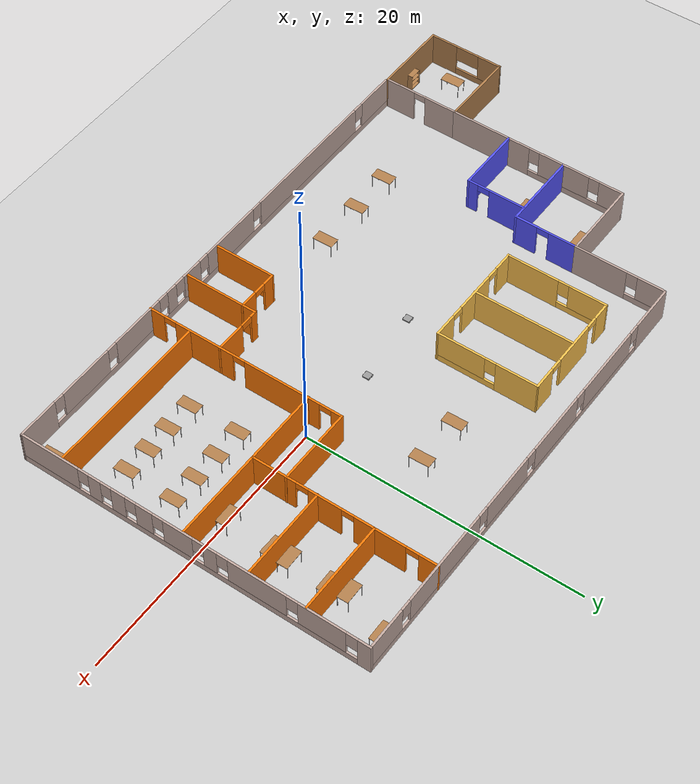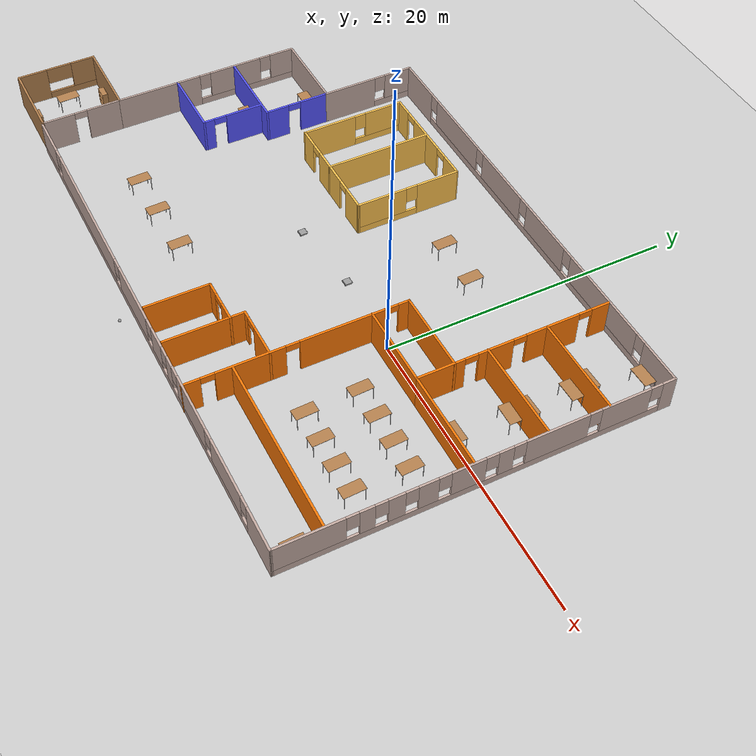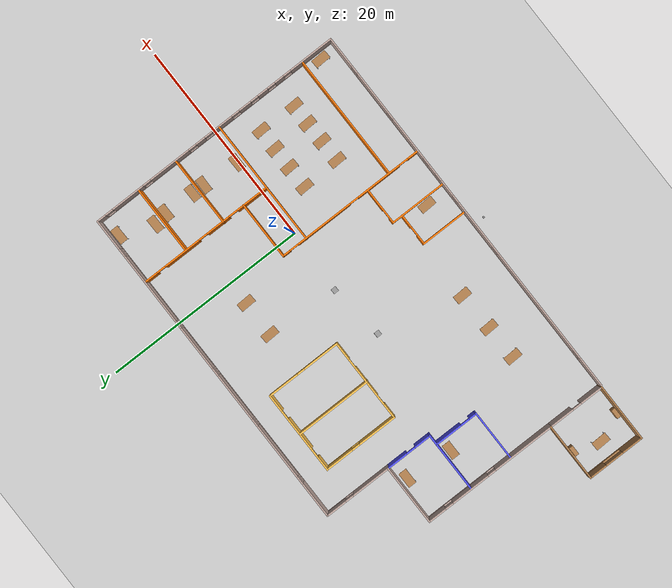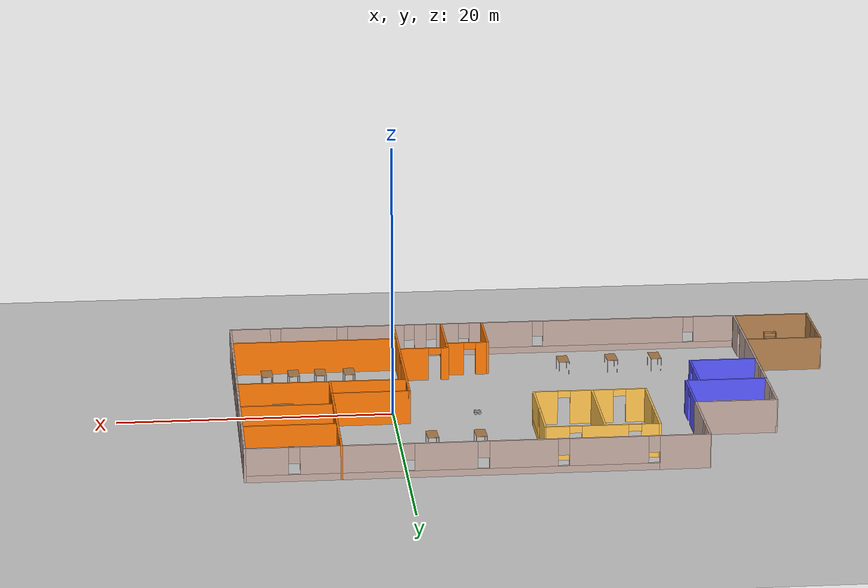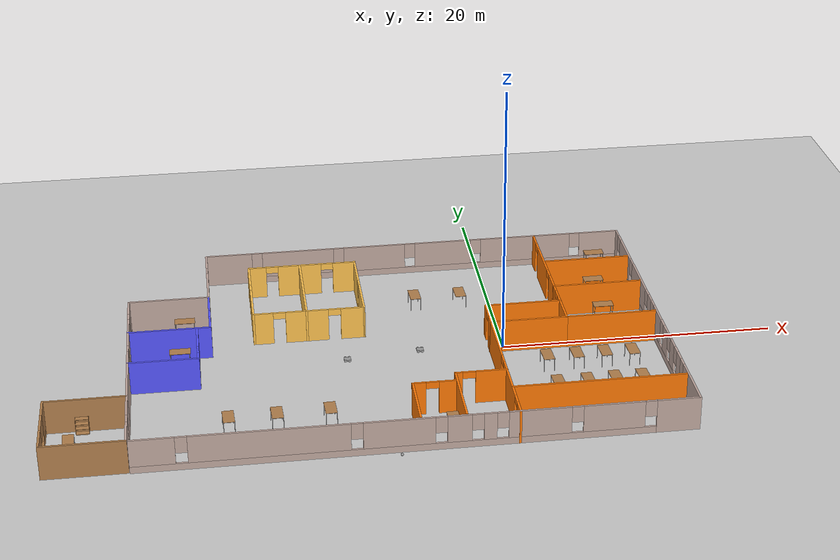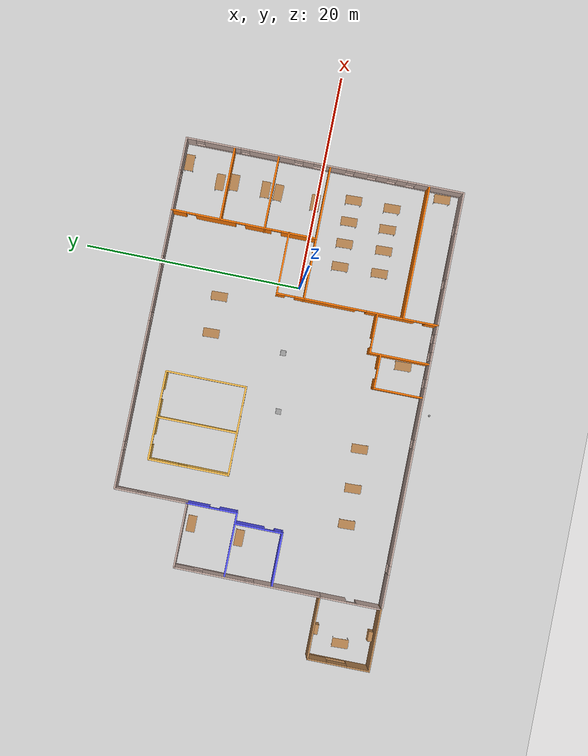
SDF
<sdf version="1.6">
 <world name="default">
  <plugin name="welcome_message" filename="libwelcome_message.so"/>
  <light name="sun" type="directional">
   <pose>0 0 10 0 -0 0</pose>
   <diffuse>0.8 0.8 0.8 1</diffuse>
   <specular>0.2 0.2 0.2 1</specular>
   <attenuation>
    <range>1000</range>
    <constant>0.9</constant>
    <linear>0.01</linear>
    <quadratic>0.001</quadratic>
   </attenuation>
   <direction>-0.5 0.1 -0.9</direction>
  </light>
  <model name="ground_plane">
   <static>1</static>
   <link name="link">
    <collision name="collision">
     <geometry><plane><normal>0 0 1</normal><size>100 100</size></plane></geometry>
     <surface><friction><ode><mu>100</mu><mu2>50</mu2></ode></friction></surface>
    </collision>
    <visual name="visual">
     <cast_shadows>0</cast_shadows>
     <geometry><plane><normal>0 0 1</normal><size>100 100</size></plane></geometry>
     <material>
      <script><uri>file://media/materials/scripts/gazebo.material</uri><name>Gazebo/Grey</name></script>
     </material>
    </visual>
   </link>
  </model>
  <gravity>0 0 -9.8</gravity>
  <magnetic_field>6e-06 2.3e-05 -4.2e-05</magnetic_field>
  <atmosphere type="adiabatic"/>
  <physics name="default_physics" default="0" type="ode">
   <max_step_size>0.001</max_step_size>
   <real_time_factor>1</real_time_factor>
   <real_time_update_rate>1000</real_time_update_rate>
  </physics>
  <scene><ambient>0.4 0.4 0.4 1</ambient><background>0.7 0.7 0.7 1</background><shadows>1</shadows></scene>
  <spherical_coordinates>
   <surface_model>EARTH_WGS84</surface_model>
   <latitude_deg>0</latitude_deg>
   <longitude_deg>0</longitude_deg>
   <elevation>0</elevation>
   <heading_deg>0</heading_deg>
  </spherical_coordinates>
  <model name="Building">
   <pose>-10.6691 -0.0294 0 0 -0 0</pose>
   <link name="Wall_158">
    <pose>5.73934 12.8407 0 0 -0 0</pose>
    <visual name="Wall_158_Visual_0">
     <pose>-14.4808 0 1.25 0 -0 0</pose>
     <geometry><box><size>3.53833 0.15 2.5</size></box></geometry>
     <material>
      <script><uri>file://media/materials/scripts/gazebo.material</uri><name>Gazebo/Grey</name></script>
      <ambient>0.760784 0.662745 0.627451 1</ambient>
     </material>
     <meta><layer>0</layer></meta>
    </visual>
    <collision name="Wall_158_Collision_0">
     <geometry><box><size>3.53833 0.15 2.5</size></box></geometry>
     <pose>-14.4808 0 1.25 0 -0 0</pose>
    </collision>
    <visual name="Wall_158_Visual_1">
     <pose>1.76917 0 0.25 0 -0 0</pose>
     <geometry><box><size>28.9617 0.15 0.5</size></box></geometry>
     <material>
      <script><uri>file://media/materials/scripts/gazebo.material</uri><name>Gazebo/Grey</name></script>
      <ambient>0.760784 0.662745 0.627451 1</ambient>
     </material>
     <meta><layer>0</layer></meta>
    </visual>
    <collision name="Wall_158_Collision_1">
     <geometry><box><size>28.9617 0.15 0.5</size></box></geometry>
     <pose>1.76917 0 0.25 0 -0 0</pose>
    </collision>
    <visual name="Wall_158_Visual_2">
     <pose>-9.14295 0 1.5 0 -0 0</pose>
     <geometry><box><size>5.53743 0.15 2</size></box></geometry>
     <material>
      <script><uri>file://media/materials/scripts/gazebo.material</uri><name>Gazebo/Grey</name></script>
      <ambient>0.760784 0.662745 0.627451 1</ambient>
     </material>
     <meta><layer>0</layer></meta>
    </visual>
    <collision name="Wall_158_Collision_2">
     <geometry><box><size>5.53743 0.15 2</size></box></geometry>
     <pose>-9.14295 0 1.5 0 -0 0</pose>
    </collision>
    <visual name="Wall_158_Visual_3">
     <pose>-3.18054 0 1.5 0 -0 0</pose>
     <geometry><box><size>4.7874 0.15 2</size></box></geometry>
     <material>
      <script><uri>file://media/materials/scripts/gazebo.material</uri><name>Gazebo/Grey</name></script>
      <ambient>0.760784 0.662745 0.627451 1</ambient>
     </material>
     <meta><layer>0</layer></meta>
    </visual>
    <collision name="Wall_158_Collision_3">
     <geometry><box><size>4.7874 0.15 2</size></box></geometry>
     <pose>-3.18054 0 1.5 0 -0 0</pose>
    </collision>
    <visual name="Wall_158_Visual_4">
     <pose>2.2199 0 1.5 0 -0 0</pose>
     <geometry><box><size>4.41347 0.15 2</size></box></geometry>
     <material>
      <script><uri>file://media/materials/scripts/gazebo.material</uri><name>Gazebo/Grey</name></script>
      <ambient>0.760784 0.662745 0.627451 1</ambient>
     </material>
     <meta><layer>0</layer></meta>
    </visual>
    <collision name="Wall_158_Collision_4">
     <geometry><box><size>4.41347 0.15 2</size></box></geometry>
     <pose>2.2199 0 1.5 0 -0 0</pose>
    </collision>
    <visual name="Wall_158_Visual_5">
     <pose>8.79242 0 1.5 0 -0 0</pose>
     <geometry><box><size>7.13158 0.15 2</size></box></geometry>
     <material>
      <script><uri>file://media/materials/scripts/gazebo.material</uri><name>Gazebo/Grey</name></script>
      <ambient>0.760784 0.662745 0.627451 1</ambient>
     </material>
     <meta><layer>0</layer></meta>
    </visual>
    <collision name="Wall_158_Collision_5">
     <geometry><box><size>7.13158 0.15 2</size></box></geometry>
     <pose>8.79242 0 1.5 0 -0 0</pose>
    </collision>
    <visual name="Wall_158_Visual_6">
     <pose>14.7041 0 1.5 0 -0 0</pose>
     <geometry><box><size>3.09179 0.15 2</size></box></geometry>
     <material>
      <script><uri>file://media/materials/scripts/gazebo.material</uri><name>Gazebo/Grey</name></script>
      <ambient>0.760784 0.662745 0.627451 1</ambient>
     </material>
     <meta><layer>0</layer></meta>
    </visual>
    <collision name="Wall_158_Collision_6">
     <geometry><box><size>3.09179 0.15 2</size></box></geometry>
     <pose>14.7041 0 1.5 0 -0 0</pose>
    </collision>
    <visual name="Wall_158_Visual_7">
     <pose>-12.3117 0 1.9 0 -0 0</pose>
     <geometry><box><size>0.8 0.15 1.2</size></box></geometry>
     <material>
      <script><uri>file://media/materials/scripts/gazebo.material</uri><name>Gazebo/Grey</name></script>
      <ambient>0.760784 0.662745 0.627451 1</ambient>
     </material>
     <meta><layer>0</layer></meta>
    </visual>
    <collision name="Wall_158_Collision_7">
     <geometry><box><size>0.8 0.15 1.2</size></box></geometry>
     <pose>-12.3117 0 1.9 0 -0 0</pose>
    </collision>
    <visual name="Wall_158_Visual_8">
     <pose>-5.97424 0 1.9 0 -0 0</pose>
     <geometry><box><size>0.8 0.15 1.2</size></box></geometry>
     <material>
      <script><uri>file://media/materials/scripts/gazebo.material</uri><name>Gazebo/Grey</name></script>
      <ambient>0.760784 0.662745 0.627451 1</ambient>
     </material>
     <meta><layer>0</layer></meta>
    </visual>
    <collision name="Wall_158_Collision_8">
     <geometry><box><size>0.8 0.15 1.2</size></box></geometry>
     <pose>-5.97424 0 1.9 0 -0 0</pose>
    </collision>
    <visual name="Wall_158_Visual_9">
     <pose>-0.386836 0 1.9 0 -0 0</pose>
     <geometry><box><size>0.8 0.15 1.2</size></box></geometry>
     <material>
      <script><uri>file://media/materials/scripts/gazebo.material</uri><name>Gazebo/Grey</name></script>
      <ambient>0.760784 0.662745 0.627451 1</ambient>
     </material>
     <meta><layer>0</layer></meta>
    </visual>
    <collision name="Wall_158_Collision_9">
     <geometry><box><size>0.8 0.15 1.2</size></box></geometry>
     <pose>-0.386836 0 1.9 0 -0 0</pose>
    </collision>
    <visual name="Wall_158_Visual_10">
     <pose>4.82663 0 1.9 0 -0 0</pose>
     <geometry><box><size>0.8 0.15 1.2</size></box></geometry>
     <material>
      <script><uri>file://media/materials/scripts/gazebo.material</uri><name>Gazebo/Grey</name></script>
      <ambient>0.760784 0.662745 0.627451 1</ambient>
     </material>
     <meta><layer>0</layer></meta>
    </visual>
    <collision name="Wall_158_Collision_10">
     <geometry><box><size>0.8 0.15 1.2</size></box></geometry>
     <pose>4.82663 0 1.9 0 -0 0</pose>
    </collision>
    <visual name="Wall_158_Visual_11">
     <pose>12.7582 0 1.9 0 -0 0</pose>
     <geometry><box><size>0.8 0.15 1.2</size></box></geometry>
     <material>
      <script><uri>file://media/materials/scripts/gazebo.material</uri><name>Gazebo/Grey</name></script>
      <ambient>0.760784 0.662745 0.627451 1</ambient>
     </material>
     <meta><layer>0</layer></meta>
    </visual>
    <collision name="Wall_158_Collision_11">
     <geometry><box><size>0.8 0.15 1.2</size></box></geometry>
     <pose>12.7582 0 1.9 0 -0 0</pose>
    </collision>
   </link>
   <link name="Wall_160">
    <pose>21.925 0.027541 0 0 0 -1.56997</pose>
    <visual name="Wall_160_Visual_0">
     <pose>-12.4183 0 1.25 0 -0 0</pose>
     <geometry><box><size>0.939904 0.15 2.5</size></box></geometry>
     <material>
      <script><uri>file://media/materials/scripts/gazebo.material</uri><name>Gazebo/Grey</name></script>
      <ambient>0.760784 0.662745 0.627451 1</ambient>
     </material>
     <meta><layer>0</layer></meta>
    </visual>
    <collision name="Wall_160_Collision_0">
     <geometry><box><size>0.939904 0.15 2.5</size></box></geometry>
     <pose>-12.4183 0 1.25 0 -0 0</pose>
    </collision>
    <visual name="Wall_160_Visual_1">
     <pose>0.469952 0 0.25 0 -0 0</pose>
     <geometry><box><size>24.8365 0.15 0.5</size></box></geometry>
     <material>
      <script><uri>file://media/materials/scripts/gazebo.material</uri><name>Gazebo/Grey</name></script>
      <ambient>0.760784 0.662745 0.627451 1</ambient>
     </material>
     <meta><layer>0</layer></meta>
    </visual>
    <collision name="Wall_160_Collision_1">
     <geometry><box><size>24.8365 0.15 0.5</size></box></geometry>
     <pose>0.469952 0 0.25 0 -0 0</pose>
    </collision>
    <visual name="Wall_160_Visual_2">
     <pose>-9.46541 0 1.5 0 -0 0</pose>
     <geometry><box><size>3.36577 0.15 2</size></box></geometry>
     <material>
      <script><uri>file://media/materials/scripts/gazebo.material</uri><name>Gazebo/Grey</name></script>
      <ambient>0.760784 0.662745 0.627451 1</ambient>
     </material>
     <meta><layer>0</layer></meta>
    </visual>
    <collision name="Wall_160_Collision_2">
     <geometry><box><size>3.36577 0.15 2</size></box></geometry>
     <pose>-9.46541 0 1.5 0 -0 0</pose>
    </collision>
    <visual name="Wall_160_Visual_3">
     <pose>-4.87743 0 1.5 0 -0 0</pose>
     <geometry><box><size>4.21019 0.15 2</size></box></geometry>
     <material>
      <script><uri>file://media/materials/scripts/gazebo.material</uri><name>Gazebo/Grey</name></script>
      <ambient>0.760784 0.662745 0.627451 1</ambient>
     </material>
     <meta><layer>0</layer></meta>
    </visual>
    <collision name="Wall_160_Collision_3">
     <geometry><box><size>4.21019 0.15 2</size></box></geometry>
     <pose>-4.87743 0 1.5 0 -0 0</pose>
    </collision>
    <visual name="Wall_160_Visual_4">
     <pose>-1.48571 0 1.5 0 -0 0</pose>
     <geometry><box><size>0.973268 0.15 2</size></box></geometry>
     <material>
      <script><uri>file://media/materials/scripts/gazebo.material</uri><name>Gazebo/Grey</name></script>
      <ambient>0.760784 0.662745 0.627451 1</ambient>
     </material>
     <meta><layer>0</layer></meta>
    </visual>
    <collision name="Wall_160_Collision_4">
     <geometry><box><size>0.973268 0.15 2</size></box></geometry>
     <pose>-1.48571 0 1.5 0 -0 0</pose>
    </collision>
    <visual name="Wall_160_Visual_5">
     <pose>0.892725 0 1.5 0 -0 0</pose>
     <geometry><box><size>2.18359 0.15 2</size></box></geometry>
     <material>
      <script><uri>file://media/materials/scripts/gazebo.material</uri><name>Gazebo/Grey</name></script>
      <ambient>0.760784 0.662745 0.627451 1</ambient>
     </material>
     <meta><layer>0</layer></meta>
    </visual>
    <collision name="Wall_160_Collision_5">
     <geometry><box><size>2.18359 0.15 2</size></box></geometry>
     <pose>0.892725 0 1.5 0 -0 0</pose>
    </collision>
    <visual name="Wall_160_Visual_6">
     <pose>3.41189 0 1.5 0 -0 0</pose>
     <geometry><box><size>1.25474 0.15 2</size></box></geometry>
     <material>
      <script><uri>file://media/materials/scripts/gazebo.material</uri><name>Gazebo/Grey</name></script>
      <ambient>0.760784 0.662745 0.627451 1</ambient>
     </material>
     <meta><layer>0</layer></meta>
    </visual>
    <collision name="Wall_160_Collision_6">
     <geometry><box><size>1.25474 0.15 2</size></box></geometry>
     <pose>3.41189 0 1.5 0 -0 0</pose>
    </collision>
    <visual name="Wall_160_Visual_7">
     <pose>5.36812 0 1.5 0 -0 0</pose>
     <geometry><box><size>1.05771 0.15 2</size></box></geometry>
     <material>
      <script><uri>file://media/materials/scripts/gazebo.material</uri><name>Gazebo/Grey</name></script>
      <ambient>0.760784 0.662745 0.627451 1</ambient>
     </material>
     <meta><layer>0</layer></meta>
    </visual>
    <collision name="Wall_160_Collision_7">
     <geometry><box><size>1.05771 0.15 2</size></box></geometry>
     <pose>5.36812 0 1.5 0 -0 0</pose>
    </collision>
    <visual name="Wall_160_Visual_8">
     <pose>7.16955 0 1.5 0 -0 0</pose>
     <geometry><box><size>0.945153 0.15 2</size></box></geometry>
     <material>
      <script><uri>file://media/materials/scripts/gazebo.material</uri><name>Gazebo/Grey</name></script>
      <ambient>0.760784 0.662745 0.627451 1</ambient>
     </material>
     <meta><layer>0</layer></meta>
    </visual>
    <collision name="Wall_160_Collision_8">
     <geometry><box><size>0.945153 0.15 2</size></box></geometry>
     <pose>7.16955 0 1.5 0 -0 0</pose>
    </collision>
    <visual name="Wall_160_Visual_9">
     <pose>10.6652 0 1.5 0 -0 0</pose>
     <geometry><box><size>4.44608 0.15 2</size></box></geometry>
     <material>
      <script><uri>file://media/materials/scripts/gazebo.material</uri><name>Gazebo/Grey</name></script>
      <ambient>0.760784 0.662745 0.627451 1</ambient>
     </material>
     <meta><layer>0</layer></meta>
    </visual>
    <collision name="Wall_160_Collision_9">
     <geometry><box><size>4.44608 0.15 2</size></box></geometry>
     <pose>10.6652 0 1.5 0 -0 0</pose>
    </collision>
    <visual name="Wall_160_Visual_10">
     <pose>-11.5483 0 1.9 0 -0 0</pose>
     <geometry><box><size>0.8 0.15 1.2</size></box></geometry>
     <material>
      <script><uri>file://media/materials/scripts/gazebo.material</uri><name>Gazebo/Grey</name></script>
      <ambient>0.760784 0.662745 0.627451 1</ambient>
     </material>
     <meta><layer>0</layer></meta>
    </visual>
    <collision name="Wall_160_Collision_10">
     <geometry><box><size>0.8 0.15 1.2</size></box></geometry>
     <pose>-11.5483 0 1.9 0 -0 0</pose>
    </collision>
    <visual name="Wall_160_Visual_11">
     <pose>-7.38253 0 1.9 0 -0 0</pose>
     <geometry><box><size>0.8 0.15 1.2</size></box></geometry>
     <material>
      <script><uri>file://media/materials/scripts/gazebo.material</uri><name>Gazebo/Grey</name></script>
      <ambient>0.760784 0.662745 0.627451 1</ambient>
     </material>
     <meta><layer>0</layer></meta>
    </visual>
    <collision name="Wall_160_Collision_11">
     <geometry><box><size>0.8 0.15 1.2</size></box></geometry>
     <pose>-7.38253 0 1.9 0 -0 0</pose>
    </collision>
    <visual name="Wall_160_Visual_12">
     <pose>-2.37234 0 1.9 0 -0 0</pose>
     <geometry><box><size>0.8 0.15 1.2</size></box></geometry>
     <material>
      <script><uri>file://media/materials/scripts/gazebo.material</uri><name>Gazebo/Grey</name></script>
      <ambient>0.760784 0.662745 0.627451 1</ambient>
     </material>
     <meta><layer>0</layer></meta>
    </visual>
    <collision name="Wall_160_Collision_12">
     <geometry><box><size>0.8 0.15 1.2</size></box></geometry>
     <pose>-2.37234 0 1.9 0 -0 0</pose>
    </collision>
    <visual name="Wall_160_Visual_13">
     <pose>-0.599072 0 1.9 0 -0 0</pose>
     <geometry><box><size>0.8 0.15 1.2</size></box></geometry>
     <material>
      <script><uri>file://media/materials/scripts/gazebo.material</uri><name>Gazebo/Grey</name></script>
      <ambient>0.760784 0.662745 0.627451 1</ambient>
     </material>
     <meta><layer>0</layer></meta>
    </visual>
    <collision name="Wall_160_Collision_13">
     <geometry><box><size>0.8 0.15 1.2</size></box></geometry>
     <pose>-0.599072 0 1.9 0 -0 0</pose>
    </collision>
    <visual name="Wall_160_Visual_14">
     <pose>2.38452 0 1.9 0 -0 0</pose>
     <geometry><box><size>0.8 0.15 1.2</size></box></geometry>
     <material>
      <script><uri>file://media/materials/scripts/gazebo.material</uri><name>Gazebo/Grey</name></script>
      <ambient>0.760784 0.662745 0.627451 1</ambient>
     </material>
     <meta><layer>0</layer></meta>
    </visual>
    <collision name="Wall_160_Collision_14">
     <geometry><box><size>0.8 0.15 1.2</size></box></geometry>
     <pose>2.38452 0 1.9 0 -0 0</pose>
    </collision>
    <visual name="Wall_160_Visual_15">
     <pose>4.43926 0 1.9 0 -0 0</pose>
     <geometry><box><size>0.8 0.15 1.2</size></box></geometry>
     <material>
      <script><uri>file://media/materials/scripts/gazebo.material</uri><name>Gazebo/Grey</name></script>
      <ambient>0.760784 0.662745 0.627451 1</ambient>
     </material>
     <meta><layer>0</layer></meta>
    </visual>
    <collision name="Wall_160_Collision_15">
     <geometry><box><size>0.8 0.15 1.2</size></box></geometry>
     <pose>4.43926 0 1.9 0 -0 0</pose>
    </collision>
    <visual name="Wall_160_Visual_16">
     <pose>6.29697 0 1.9 0 -0 0</pose>
     <geometry><box><size>0.8 0.15 1.2</size></box></geometry>
     <material>
      <script><uri>file://media/materials/scripts/gazebo.material</uri><name>Gazebo/Grey</name></script>
      <ambient>0.760784 0.662745 0.627451 1</ambient>
     </material>
     <meta><layer>0</layer></meta>
    </visual>
    <collision name="Wall_160_Collision_16">
     <geometry><box><size>0.8 0.15 1.2</size></box></geometry>
     <pose>6.29697 0 1.9 0 -0 0</pose>
    </collision>
    <visual name="Wall_160_Visual_17">
     <pose>8.04212 0 1.9 0 -0 0</pose>
     <geometry><box><size>0.8 0.15 1.2</size></box></geometry>
     <material>
      <script><uri>file://media/materials/scripts/gazebo.material</uri><name>Gazebo/Grey</name></script>
      <ambient>0.760784 0.662745 0.627451 1</ambient>
     </material>
     <meta><layer>0</layer></meta>
    </visual>
    <collision name="Wall_160_Collision_17">
     <geometry><box><size>0.8 0.15 1.2</size></box></geometry>
     <pose>8.04212 0 1.9 0 -0 0</pose>
    </collision>
   </link>
   <link name="Wall_161">
    <pose>2.8856 -12.8282 0 0 -0 3.14159</pose>
    <visual name="Wall_161_Visual_0">
     <pose>-17.595 0 1.25 0 -0 0</pose>
     <geometry><box><size>3.06004 0.15 2.5</size></box></geometry>
     <material>
      <script><uri>file://media/materials/scripts/gazebo.material</uri><name>Gazebo/Grey</name></script>
      <ambient>0.760784 0.662745 0.627451 1</ambient>
     </material>
     <meta><layer>0</layer></meta>
    </visual>
    <collision name="Wall_161_Collision_0">
     <geometry><box><size>3.06004 0.15 2.5</size></box></geometry>
     <pose>-17.595 0 1.25 0 -0 0</pose>
    </collision>
    <visual name="Wall_161_Visual_1">
     <pose>1.53002 0 0.25 0 -0 0</pose>
     <geometry><box><size>35.19 0.15 0.5</size></box></geometry>
     <material>
      <script><uri>file://media/materials/scripts/gazebo.material</uri><name>Gazebo/Grey</name></script>
      <ambient>0.760784 0.662745 0.627451 1</ambient>
     </material>
     <meta><layer>0</layer></meta>
    </visual>
    <collision name="Wall_161_Collision_1">
     <geometry><box><size>35.19 0.15 0.5</size></box></geometry>
     <pose>1.53002 0 0.25 0 -0 0</pose>
    </collision>
    <visual name="Wall_161_Visual_2">
     <pose>-13.1526 0 1.5 0 -0 0</pose>
     <geometry><box><size>4.22475 0.15 2</size></box></geometry>
     <material>
      <script><uri>file://media/materials/scripts/gazebo.material</uri><name>Gazebo/Grey</name></script>
      <ambient>0.760784 0.662745 0.627451 1</ambient>
     </material>
     <meta><layer>0</layer></meta>
    </visual>
    <collision name="Wall_161_Collision_2">
     <geometry><box><size>4.22475 0.15 2</size></box></geometry>
     <pose>-13.1526 0 1.5 0 -0 0</pose>
    </collision>
    <visual name="Wall_161_Visual_3">
     <pose>-8.105 0 1.5 0 -0 0</pose>
     <geometry><box><size>4.27041 0.15 2</size></box></geometry>
     <material>
      <script><uri>file://media/materials/scripts/gazebo.material</uri><name>Gazebo/Grey</name></script>
      <ambient>0.760784 0.662745 0.627451 1</ambient>
     </material>
     <meta><layer>0</layer></meta>
    </visual>
    <collision name="Wall_161_Collision_3">
     <geometry><box><size>4.27041 0.15 2</size></box></geometry>
     <pose>-8.105 0 1.5 0 -0 0</pose>
    </collision>
    <visual name="Wall_161_Visual_4">
     <pose>-4.73361 0 1.5 0 -0 0</pose>
     <geometry><box><size>0.872362 0.15 2</size></box></geometry>
     <material>
      <script><uri>file://media/materials/scripts/gazebo.material</uri><name>Gazebo/Grey</name></script>
      <ambient>0.760784 0.662745 0.627451 1</ambient>
     </material>
     <meta><layer>0</layer></meta>
    </visual>
    <collision name="Wall_161_Collision_4">
     <geometry><box><size>0.872362 0.15 2</size></box></geometry>
     <pose>-4.73361 0 1.5 0 -0 0</pose>
    </collision>
    <visual name="Wall_161_Visual_5">
     <pose>-2.66754 0 1.5 0 -0 0</pose>
     <geometry><box><size>1.65978 0.15 2</size></box></geometry>
     <material>
      <script><uri>file://media/materials/scripts/gazebo.material</uri><name>Gazebo/Grey</name></script>
      <ambient>0.760784 0.662745 0.627451 1</ambient>
     </material>
     <meta><layer>0</layer></meta>
    </visual>
    <collision name="Wall_161_Collision_5">
     <geometry><box><size>1.65978 0.15 2</size></box></geometry>
     <pose>-2.66754 0 1.5 0 -0 0</pose>
    </collision>
    <visual name="Wall_161_Visual_6">
     <pose>1.37416 0 1.5 0 -0 0</pose>
     <geometry><box><size>4.82362 0.15 2</size></box></geometry>
     <material>
      <script><uri>file://media/materials/scripts/gazebo.material</uri><name>Gazebo/Grey</name></script>
      <ambient>0.760784 0.662745 0.627451 1</ambient>
     </material>
     <meta><layer>0</layer></meta>
    </visual>
    <collision name="Wall_161_Collision_6">
     <geometry><box><size>4.82362 0.15 2</size></box></geometry>
     <pose>1.37416 0 1.5 0 -0 0</pose>
    </collision>
    <visual name="Wall_161_Visual_7">
     <pose>9.94407 0 1.5 0 -0 0</pose>
     <geometry><box><size>10.7162 0.15 2</size></box></geometry>
     <material>
      <script><uri>file://media/materials/scripts/gazebo.material</uri><name>Gazebo/Grey</name></script>
      <ambient>0.760784 0.662745 0.627451 1</ambient>
     </material>
     <meta><layer>0</layer></meta>
    </visual>
    <collision name="Wall_161_Collision_7">
     <geometry><box><size>10.7162 0.15 2</size></box></geometry>
     <pose>9.94407 0 1.5 0 -0 0</pose>
    </collision>
    <visual name="Wall_161_Visual_8">
     <pose>17.6136 0 1.5 0 -0 0</pose>
     <geometry><box><size>3.02283 0.15 2</size></box></geometry>
     <material>
      <script><uri>file://media/materials/scripts/gazebo.material</uri><name>Gazebo/Grey</name></script>
      <ambient>0.760784 0.662745 0.627451 1</ambient>
     </material>
     <meta><layer>0</layer></meta>
    </visual>
    <collision name="Wall_161_Collision_8">
     <geometry><box><size>3.02283 0.15 2</size></box></geometry>
     <pose>17.6136 0 1.5 0 -0 0</pose>
    </collision>
    <visual name="Wall_161_Visual_9">
     <pose>-15.665 0 1.9 0 -0 0</pose>
     <geometry><box><size>0.8 0.15 1.2</size></box></geometry>
     <material>
      <script><uri>file://media/materials/scripts/gazebo.material</uri><name>Gazebo/Grey</name></script>
      <ambient>0.760784 0.662745 0.627451 1</ambient>
     </material>
     <meta><layer>0</layer></meta>
    </visual>
    <collision name="Wall_161_Collision_9">
     <geometry><box><size>0.8 0.15 1.2</size></box></geometry>
     <pose>-15.665 0 1.9 0 -0 0</pose>
    </collision>
    <visual name="Wall_161_Visual_10">
     <pose>-10.6402 0 1.9 0 -0 0</pose>
     <geometry><box><size>0.8 0.15 1.2</size></box></geometry>
     <material>
      <script><uri>file://media/materials/scripts/gazebo.material</uri><name>Gazebo/Grey</name></script>
      <ambient>0.760784 0.662745 0.627451 1</ambient>
     </material>
     <meta><layer>0</layer></meta>
    </visual>
    <collision name="Wall_161_Collision_10">
     <geometry><box><size>0.8 0.15 1.2</size></box></geometry>
     <pose>-10.6402 0 1.9 0 -0 0</pose>
    </collision>
    <visual name="Wall_161_Visual_11">
     <pose>-5.56979 0 1.9 0 -0 0</pose>
     <geometry><box><size>0.8 0.15 1.2</size></box></geometry>
     <material>
      <script><uri>file://media/materials/scripts/gazebo.material</uri><name>Gazebo/Grey</name></script>
      <ambient>0.760784 0.662745 0.627451 1</ambient>
     </material>
     <meta><layer>0</layer></meta>
    </visual>
    <collision name="Wall_161_Collision_11">
     <geometry><box><size>0.8 0.15 1.2</size></box></geometry>
     <pose>-5.56979 0 1.9 0 -0 0</pose>
    </collision>
    <visual name="Wall_161_Visual_12">
     <pose>-3.89743 0 1.9 0 -0 0</pose>
     <geometry><box><size>0.8 0.15 1.2</size></box></geometry>
     <material>
      <script><uri>file://media/materials/scripts/gazebo.material</uri><name>Gazebo/Grey</name></script>
      <ambient>0.760784 0.662745 0.627451 1</ambient>
     </material>
     <meta><layer>0</layer></meta>
    </visual>
    <collision name="Wall_161_Collision_12">
     <geometry><box><size>0.8 0.15 1.2</size></box></geometry>
     <pose>-3.89743 0 1.9 0 -0 0</pose>
    </collision>
    <visual name="Wall_161_Visual_13">
     <pose>-1.43765 0 1.9 0 -0 0</pose>
     <geometry><box><size>0.8 0.15 1.2</size></box></geometry>
     <material>
      <script><uri>file://media/materials/scripts/gazebo.material</uri><name>Gazebo/Grey</name></script>
      <ambient>0.760784 0.662745 0.627451 1</ambient>
     </material>
     <meta><layer>0</layer></meta>
    </visual>
    <collision name="Wall_161_Collision_13">
     <geometry><box><size>0.8 0.15 1.2</size></box></geometry>
     <pose>-1.43765 0 1.9 0 -0 0</pose>
    </collision>
    <visual name="Wall_161_Visual_14">
     <pose>4.18597 0 1.9 0 -0 0</pose>
     <geometry><box><size>0.8 0.15 1.2</size></box></geometry>
     <material>
      <script><uri>file://media/materials/scripts/gazebo.material</uri><name>Gazebo/Grey</name></script>
      <ambient>0.760784 0.662745 0.627451 1</ambient>
     </material>
     <meta><layer>0</layer></meta>
    </visual>
    <collision name="Wall_161_Collision_14">
     <geometry><box><size>0.8 0.15 1.2</size></box></geometry>
     <pose>4.18597 0 1.9 0 -0 0</pose>
    </collision>
    <visual name="Wall_161_Visual_15">
     <pose>15.7022 0 1.9 0 -0 0</pose>
     <geometry><box><size>0.8 0.15 1.2</size></box></geometry>
     <material>
      <script><uri>file://media/materials/scripts/gazebo.material</uri><name>Gazebo/Grey</name></script>
      <ambient>0.760784 0.662745 0.627451 1</ambient>
     </material>
     <meta><layer>0</layer></meta>
    </visual>
    <collision name="Wall_161_Collision_15">
     <geometry><box><size>0.8 0.15 1.2</size></box></geometry>
     <pose>15.7022 0 1.9 0 -0 0</pose>
    </collision>
   </link>
   <link name="Wall_163">
    <collision name="Wall_163_Collision">
     <geometry><box><size>5.75 0.15 2.5</size></box></geometry>
     <pose>0 0 1.25 0 -0 0</pose>
    </collision>
    <visual name="Wall_163_Visual">
     <pose>0 0 1.25 0 -0 0</pose>
     <geometry><box><size>5.75 0.15 2.5</size></box></geometry>
     <material>
      <script><uri>file://media/materials/scripts/gazebo.material</uri><name>Gazebo/Wood</name></script>
      <ambient>0.760784 0.662745 0.627451 1</ambient>
     </material>
     <meta><layer>0</layer></meta>
    </visual>
    <pose>-19.1357 -7.15926 0 0 -0 0</pose>
   </link>
   <link name="Wall_164">
    <pose>-16.3357 -0.484261 0 0 -0 1.5708</pose>
    <visual name="Wall_164_Visual_0">
     <pose>-3.67658 0 1.25 0 -0 0</pose>
     <geometry><box><size>6.14683 0.15 2.5</size></box></geometry>
     <material>
      <script><uri>file://media/materials/scripts/gazebo.material</uri><name>Gazebo/Grey</name></script>
      <ambient>0.760784 0.662745 0.627451 1</ambient>
     </material>
     <meta><layer>0</layer></meta>
    </visual>
    <collision name="Wall_164_Collision_0">
     <geometry><box><size>6.14683 0.15 2.5</size></box></geometry>
     <pose>-3.67658 0 1.25 0 -0 0</pose>
    </collision>
    <visual name="Wall_164_Visual_1">
     <pose>3.07342 0 0.25 0 -0 0</pose>
     <geometry><box><size>7.35317 0.15 0.5</size></box></geometry>
     <material>
      <script><uri>file://media/materials/scripts/gazebo.material</uri><name>Gazebo/Grey</name></script>
      <ambient>0.760784 0.662745 0.627451 1</ambient>
     </material>
     <meta><layer>0</layer></meta>
    </visual>
    <collision name="Wall_164_Collision_1">
     <geometry><box><size>7.35317 0.15 0.5</size></box></geometry>
     <pose>3.07342 0 0.25 0 -0 0</pose>
    </collision>
    <visual name="Wall_164_Visual_2">
     <pose>2.14621 0 1.5 0 -0 0</pose>
     <geometry><box><size>3.89875 0.15 2</size></box></geometry>
     <material>
      <script><uri>file://media/materials/scripts/gazebo.material</uri><name>Gazebo/Grey</name></script>
      <ambient>0.760784 0.662745 0.627451 1</ambient>
     </material>
     <meta><layer>0</layer></meta>
    </visual>
    <collision name="Wall_164_Collision_2">
     <geometry><box><size>3.89875 0.15 2</size></box></geometry>
     <pose>2.14621 0 1.5 0 -0 0</pose>
    </collision>
    <visual name="Wall_164_Visual_3">
     <pose>5.82279 0 1.5 0 -0 0</pose>
     <geometry><box><size>1.85441 0.15 2</size></box></geometry>
     <material>
      <script><uri>file://media/materials/scripts/gazebo.material</uri><name>Gazebo/Grey</name></script>
      <ambient>0.760784 0.662745 0.627451 1</ambient>
     </material>
     <meta><layer>0</layer></meta>
    </visual>
    <collision name="Wall_164_Collision_3">
     <geometry><box><size>1.85441 0.15 2</size></box></geometry>
     <pose>5.82279 0 1.5 0 -0 0</pose>
    </collision>
    <visual name="Wall_164_Visual_4">
     <pose>-0.203166 0 1.9 0 -0 0</pose>
     <geometry><box><size>0.8 0.15 1.2</size></box></geometry>
     <material>
      <script><uri>file://media/materials/scripts/gazebo.material</uri><name>Gazebo/Grey</name></script>
      <ambient>0.760784 0.662745 0.627451 1</ambient>
     </material>
     <meta><layer>0</layer></meta>
    </visual>
    <collision name="Wall_164_Collision_4">
     <geometry><box><size>0.8 0.15 1.2</size></box></geometry>
     <pose>-0.203166 0 1.9 0 -0 0</pose>
    </collision>
    <visual name="Wall_164_Visual_5">
     <pose>4.49559 0 1.9 0 -0 0</pose>
     <geometry><box><size>0.8 0.15 1.2</size></box></geometry>
     <material>
      <script><uri>file://media/materials/scripts/gazebo.material</uri><name>Gazebo/Grey</name></script>
      <ambient>0.760784 0.662745 0.627451 1</ambient>
     </material>
     <meta><layer>0</layer></meta>
    </visual>
    <collision name="Wall_164_Collision_5">
     <geometry><box><size>0.8 0.15 1.2</size></box></geometry>
     <pose>4.49559 0 1.9 0 -0 0</pose>
    </collision>
   </link>
   <link name="Wall_165">
    <collision name="Wall_165_Collision">
     <geometry><box><size>6 0.15 2.5</size></box></geometry>
     <pose>0 0 1.25 0 -0 0</pose>
    </collision>
    <visual name="Wall_165_Visual">
     <pose>0 0 1.25 0 -0 0</pose>
     <geometry><box><size>6 0.15 2.5</size></box></geometry>
     <material>
      <script><uri>file://media/materials/scripts/gazebo.material</uri><name>Gazebo/Grey</name></script>
      <ambient>0.760784 0.662745 0.627451 1</ambient>
     </material>
     <meta><layer>0</layer></meta>
    </visual>
    <pose>-13.4107 6.19074 0 0 -0 0</pose>
   </link>
   <link name="Wall_166">
    <pose>-10.4857 9.49074 0 0 -0 1.5708</pose>
    <visual name="Wall_166_Visual_0">
     <pose>-1.42072 0 1.25 0 -0 0</pose>
     <geometry><box><size>3.90856 0.15 2.5</size></box></geometry>
     <material>
      <script><uri>file://media/materials/scripts/gazebo.material</uri><name>Gazebo/Grey</name></script>
      <ambient>0.760784 0.662745 0.627451 1</ambient>
     </material>
     <meta><layer>0</layer></meta>
    </visual>
    <collision name="Wall_166_Collision_0">
     <geometry><box><size>3.90856 0.15 2.5</size></box></geometry>
     <pose>-1.42072 0 1.25 0 -0 0</pose>
    </collision>
    <visual name="Wall_166_Visual_1">
     <pose>1.95428 0 0.25 0 -0 0</pose>
     <geometry><box><size>2.84144 0.15 0.5</size></box></geometry>
     <material>
      <script><uri>file://media/materials/scripts/gazebo.material</uri><name>Gazebo/Grey</name></script>
      <ambient>0.760784 0.662745 0.627451 1</ambient>
     </material>
     <meta><layer>0</layer></meta>
    </visual>
    <collision name="Wall_166_Collision_1">
     <geometry><box><size>2.84144 0.15 0.5</size></box></geometry>
     <pose>1.95428 0 0.25 0 -0 0</pose>
    </collision>
    <visual name="Wall_166_Visual_2">
     <pose>2.35428 0 1.5 0 -0 0</pose>
     <geometry><box><size>2.04144 0.15 2</size></box></geometry>
     <material>
      <script><uri>file://media/materials/scripts/gazebo.material</uri><name>Gazebo/Grey</name></script>
      <ambient>0.760784 0.662745 0.627451 1</ambient>
     </material>
     <meta><layer>0</layer></meta>
    </visual>
    <collision name="Wall_166_Collision_2">
     <geometry><box><size>2.04144 0.15 2</size></box></geometry>
     <pose>2.35428 0 1.5 0 -0 0</pose>
    </collision>
    <visual name="Wall_166_Visual_3">
     <pose>0.933557 0 1.9 0 -0 0</pose>
     <geometry><box><size>0.8 0.15 1.2</size></box></geometry>
     <material>
      <script><uri>file://media/materials/scripts/gazebo.material</uri><name>Gazebo/Grey</name></script>
      <ambient>0.760784 0.662745 0.627451 1</ambient>
     </material>
     <meta><layer>0</layer></meta>
    </visual>
    <collision name="Wall_166_Collision_3">
     <geometry><box><size>0.8 0.15 1.2</size></box></geometry>
     <pose>0.933557 0 1.9 0 -0 0</pose>
    </collision>
   </link>
   <link name="Wall_168">
    <pose>15.2204 6.16765 0 0 0 -1.5708</pose>
    <visual name="Wall_168_Visual_0">
     <pose>-6.05122 0 1.25 0 -0 0</pose>
     <geometry><box><size>1.39756 0.15 2.5</size></box></geometry>
     <material>
      <script><uri>file://media/materials/scripts/gazebo.material</uri><name>Gazebo/Grey</name></script>
      <ambient>0.996078 0.47451 0.0196078 1</ambient>
     </material>
     <meta><layer>0</layer></meta>
    </visual>
    <collision name="Wall_168_Collision_0">
     <geometry><box><size>1.39756 0.15 2.5</size></box></geometry>
     <pose>-6.05122 0 1.25 0 -0 0</pose>
    </collision>
    <visual name="Wall_168_Visual_1">
     <pose>-2.60621 0 1.25 0 -0 0</pose>
     <geometry><box><size>3.69245 0.15 2.5</size></box></geometry>
     <material>
      <script><uri>file://media/materials/scripts/gazebo.material</uri><name>Gazebo/Grey</name></script>
      <ambient>0.996078 0.47451 0.0196078 1</ambient>
     </material>
     <meta><layer>0</layer></meta>
    </visual>
    <collision name="Wall_168_Collision_1">
     <geometry><box><size>3.69245 0.15 2.5</size></box></geometry>
     <pose>-2.60621 0 1.25 0 -0 0</pose>
    </collision>
    <visual name="Wall_168_Visual_2">
     <pose>1.3484 0 1.25 0 -0 0</pose>
     <geometry><box><size>2.41677 0.15 2.5</size></box></geometry>
     <material>
      <script><uri>file://media/materials/scripts/gazebo.material</uri><name>Gazebo/Grey</name></script>
      <ambient>0.996078 0.47451 0.0196078 1</ambient>
     </material>
     <meta><layer>0</layer></meta>
    </visual>
    <collision name="Wall_168_Collision_2">
     <geometry><box><size>2.41677 0.15 2.5</size></box></geometry>
     <pose>1.3484 0 1.25 0 -0 0</pose>
    </collision>
    <visual name="Wall_168_Visual_3">
     <pose>5.10339 0 1.25 0 -0 0</pose>
     <geometry><box><size>3.29322 0.15 2.5</size></box></geometry>
     <material>
      <script><uri>file://media/materials/scripts/gazebo.material</uri><name>Gazebo/Grey</name></script>
      <ambient>0.996078 0.47451 0.0196078 1</ambient>
     </material>
     <meta><layer>0</layer></meta>
    </visual>
    <collision name="Wall_168_Collision_3">
     <geometry><box><size>3.29322 0.15 2.5</size></box></geometry>
     <pose>5.10339 0 1.25 0 -0 0</pose>
    </collision>
    <visual name="Wall_168_Visual_4">
     <pose>-4.90244 0 2.25 0 -0 0</pose>
     <geometry><box><size>0.9 0.15 0.5</size></box></geometry>
     <material>
      <script><uri>file://media/materials/scripts/gazebo.material</uri><name>Gazebo/Grey</name></script>
      <ambient>0.996078 0.47451 0.0196078 1</ambient>
     </material>
     <meta><layer>0</layer></meta>
    </visual>
    <collision name="Wall_168_Collision_4">
     <geometry><box><size>0.9 0.15 0.5</size></box></geometry>
     <pose>-4.90244 0 2.25 0 -0 0</pose>
    </collision>
    <visual name="Wall_168_Visual_5">
     <pose>-0.309989 0 2.25 0 -0 0</pose>
     <geometry><box><size>0.9 0.15 0.5</size></box></geometry>
     <material>
      <script><uri>file://media/materials/scripts/gazebo.material</uri><name>Gazebo/Grey</name></script>
      <ambient>0.996078 0.47451 0.0196078 1</ambient>
     </material>
     <meta><layer>0</layer></meta>
    </visual>
    <collision name="Wall_168_Collision_5">
     <geometry><box><size>0.9 0.15 0.5</size></box></geometry>
     <pose>-0.309989 0 2.25 0 -0 0</pose>
    </collision>
    <visual name="Wall_168_Visual_6">
     <pose>3.00678 0 2.25 0 -0 0</pose>
     <geometry><box><size>0.9 0.15 0.5</size></box></geometry>
     <material>
      <script><uri>file://media/materials/scripts/gazebo.material</uri><name>Gazebo/Grey</name></script>
      <ambient>0.996078 0.47451 0.0196078 1</ambient>
     </material>
     <meta><layer>0</layer></meta>
    </visual>
    <collision name="Wall_168_Collision_6">
     <geometry><box><size>0.9 0.15 0.5</size></box></geometry>
     <pose>3.00678 0 2.25 0 -0 0</pose>
    </collision>
   </link>
   <link name="Wall_169">
    <collision name="Wall_169_Collision">
     <geometry><box><size>6.75 0.15 2.5</size></box></geometry>
     <pose>0 0 1.25 0 -0 0</pose>
    </collision>
    <visual name="Wall_169_Visual">
     <pose>0 0 1.25 0 -0 0</pose>
     <geometry><box><size>6.75 0.15 2.5</size></box></geometry>
     <material>
      <script><uri>file://media/materials/scripts/gazebo.material</uri><name>Gazebo/Grey</name></script>
      <ambient>0.996078 0.47451 0.0196078 1</ambient>
     </material>
     <meta><layer>0</layer></meta>
    </visual>
    <pose>18.5204 -0.507347 0 0 -0 0</pose>
   </link>
   <link name="Wall_171">
    <collision name="Wall_171_Collision">
     <geometry><box><size>6.75 0.15 2.5</size></box></geometry>
     <pose>0 0 1.25 0 -0 0</pose>
    </collision>
    <visual name="Wall_171_Visual">
     <pose>0 0 1.25 0 -0 0</pose>
     <geometry><box><size>6.75 0.15 2.5</size></box></geometry>
     <material>
      <script><uri>file://media/materials/scripts/gazebo.material</uri><name>Gazebo/Grey</name></script>
      <ambient>0.996078 0.47451 0.0196078 1</ambient>
     </material>
     <meta><layer>0</layer></meta>
    </visual>
    <pose>18.5682 8.3698 0 0 -0 0</pose>
   </link>
   <link name="Wall_173">
    <collision name="Wall_173_Collision">
     <geometry><box><size>6.75 0.15 2.5</size></box></geometry>
     <pose>0 0 1.25 0 -0 0</pose>
    </collision>
    <visual name="Wall_173_Visual">
     <pose>0 0 1.25 0 -0 0</pose>
     <geometry><box><size>6.75 0.15 2.5</size></box></geometry>
     <material>
      <script><uri>file://media/materials/scripts/gazebo.material</uri><name>Gazebo/Grey</name></script>
      <ambient>0.996078 0.47451 0.0196078 1</ambient>
     </material>
     <meta><layer>0</layer></meta>
    </visual>
    <pose>18.4965 4.27965 0 0 -0 0</pose>
   </link>
   <link name="Wall_176">
    <collision name="Wall_176_Collision">
     <geometry><box><size>5.75 0.15 2.5</size></box></geometry>
     <pose>0 0 1.25 0 -0 0</pose>
    </collision>
    <visual name="Wall_176_Visual">
     <pose>0 0 1.25 0 -0 0</pose>
     <geometry><box><size>5.75 0.15 2.5</size></box></geometry>
     <material>
      <script><uri>file://media/materials/scripts/gazebo.material</uri><name>Gazebo/Grey</name></script>
      <ambient>0.996078 0.47451 0.0196078 1</ambient>
     </material>
     <meta><layer>0</layer></meta>
    </visual>
    <pose>12.4443 2.00735 0 0 -0 3.14159</pose>
   </link>
   <link name="Wall_177">
    <pose>9.64433 -5.41765 0 0 0 -1.5708</pose>
    <visual name="Wall_177_Visual_0">
     <pose>-7.08426 0 1.25 0 -0 0</pose>
     <geometry><box><size>0.83148 0.15 2.5</size></box></geometry>
     <material>
      <script><uri>file://media/materials/scripts/gazebo.material</uri><name>Gazebo/Grey</name></script>
      <ambient>0.996078 0.47451 0.0196078 1</ambient>
     </material>
     <meta><layer>0</layer></meta>
    </visual>
    <collision name="Wall_177_Collision_0">
     <geometry><box><size>0.83148 0.15 2.5</size></box></geometry>
     <pose>-7.08426 0 1.25 0 -0 0</pose>
    </collision>
    <visual name="Wall_177_Visual_1">
     <pose>-2.91238 0 1.25 0 -0 0</pose>
     <geometry><box><size>5.71227 0.15 2.5</size></box></geometry>
     <material>
      <script><uri>file://media/materials/scripts/gazebo.material</uri><name>Gazebo/Grey</name></script>
      <ambient>0.996078 0.47451 0.0196078 1</ambient>
     </material>
     <meta><layer>0</layer></meta>
    </visual>
    <collision name="Wall_177_Collision_1">
     <geometry><box><size>5.71227 0.15 2.5</size></box></geometry>
     <pose>-2.91238 0 1.25 0 -0 0</pose>
    </collision>
    <visual name="Wall_177_Visual_2">
     <pose>3.11521 0 1.25 0 -0 0</pose>
     <geometry><box><size>4.5429 0.15 2.5</size></box></geometry>
     <material>
      <script><uri>file://media/materials/scripts/gazebo.material</uri><name>Gazebo/Grey</name></script>
      <ambient>0.996078 0.47451 0.0196078 1</ambient>
     </material>
     <meta><layer>0</layer></meta>
    </visual>
    <collision name="Wall_177_Collision_2">
     <geometry><box><size>4.5429 0.15 2.5</size></box></geometry>
     <pose>3.11521 0 1.25 0 -0 0</pose>
    </collision>
    <visual name="Wall_177_Visual_3">
     <pose>6.89333 0 1.25 0 -0 0</pose>
     <geometry><box><size>1.21334 0.15 2.5</size></box></geometry>
     <material>
      <script><uri>file://media/materials/scripts/gazebo.material</uri><name>Gazebo/Grey</name></script>
      <ambient>0.996078 0.47451 0.0196078 1</ambient>
     </material>
     <meta><layer>0</layer></meta>
    </visual>
    <collision name="Wall_177_Collision_3">
     <geometry><box><size>1.21334 0.15 2.5</size></box></geometry>
     <pose>6.89333 0 1.25 0 -0 0</pose>
    </collision>
    <visual name="Wall_177_Visual_4">
     <pose>-6.21852 0 2.25 0 -0 0</pose>
     <geometry><box><size>0.9 0.15 0.5</size></box></geometry>
     <material>
      <script><uri>file://media/materials/scripts/gazebo.material</uri><name>Gazebo/Grey</name></script>
      <ambient>0.996078 0.47451 0.0196078 1</ambient>
     </material>
     <meta><layer>0</layer></meta>
    </visual>
    <collision name="Wall_177_Collision_4">
     <geometry><box><size>0.9 0.15 0.5</size></box></geometry>
     <pose>-6.21852 0 2.25 0 -0 0</pose>
    </collision>
    <visual name="Wall_177_Visual_5">
     <pose>0.393754 0 2.25 0 -0 0</pose>
     <geometry><box><size>0.9 0.15 0.5</size></box></geometry>
     <material>
      <script><uri>file://media/materials/scripts/gazebo.material</uri><name>Gazebo/Grey</name></script>
      <ambient>0.996078 0.47451 0.0196078 1</ambient>
     </material>
     <meta><layer>0</layer></meta>
    </visual>
    <collision name="Wall_177_Collision_5">
     <geometry><box><size>0.9 0.15 0.5</size></box></geometry>
     <pose>0.393754 0 2.25 0 -0 0</pose>
    </collision>
    <visual name="Wall_177_Visual_6">
     <pose>5.83666 0 2.25 0 -0 0</pose>
     <geometry><box><size>0.9 0.15 0.5</size></box></geometry>
     <material>
      <script><uri>file://media/materials/scripts/gazebo.material</uri><name>Gazebo/Grey</name></script>
      <ambient>0.996078 0.47451 0.0196078 1</ambient>
     </material>
     <meta><layer>0</layer></meta>
    </visual>
    <collision name="Wall_177_Collision_6">
     <geometry><box><size>0.9 0.15 0.5</size></box></geometry>
     <pose>5.83666 0 2.25 0 -0 0</pose>
    </collision>
   </link>
   <link name="Wall_179">
    <collision name="Wall_179_Collision">
     <geometry><box><size>5.75 0.15 2.5</size></box></geometry>
     <pose>0 0 1.25 0 -0 0</pose>
    </collision>
    <visual name="Wall_179_Visual">
     <pose>0 0 1.25 0 -0 0</pose>
     <geometry><box><size>5.75 0.15 2.5</size></box></geometry>
     <material>
      <script><uri>file://media/materials/scripts/gazebo.material</uri><name>Gazebo/Grey</name></script>
      <ambient>0.996078 0.47451 0.0196078 1</ambient>
     </material>
     <meta><layer>0</layer></meta>
    </visual>
    <pose>12.4204 -0.507347 0 0 -0 3.14159</pose>
   </link>
   <link name="Wall_181">
    <collision name="Wall_181_Collision">
     <geometry><box><size>12.25 0.15 2.5</size></box></geometry>
     <pose>0 0 1.25 0 -0 0</pose>
    </collision>
    <visual name="Wall_181_Visual">
     <pose>0 0 1.25 0 -0 0</pose>
     <geometry><box><size>12.25 0.15 2.5</size></box></geometry>
     <material>
      <script><uri>file://media/materials/scripts/gazebo.material</uri><name>Gazebo/Grey</name></script>
      <ambient>0.996078 0.47451 0.0196078 1</ambient>
     </material>
     <meta><layer>0</layer></meta>
    </visual>
    <pose>15.7415 -9.67071 0 0 -0 0</pose>
   </link>
   <link name="Wall_183">
    <pose>7.84956 -7.30115 0 0 -0 3.14159</pose>
    <visual name="Wall_183_Visual_0">
     <pose>-0.737336 0 1.25 0 -0 0</pose>
     <geometry><box><size>2.27533 0.15 2.5</size></box></geometry>
     <material>
      <script><uri>file://media/materials/scripts/gazebo.material</uri><name>Gazebo/Grey</name></script>
      <ambient>0.996078 0.47451 0.0196078 1</ambient>
     </material>
     <meta><layer>0</layer></meta>
    </visual>
    <collision name="Wall_183_Collision_0">
     <geometry><box><size>2.27533 0.15 2.5</size></box></geometry>
     <pose>-0.737336 0 1.25 0 -0 0</pose>
    </collision>
    <visual name="Wall_183_Visual_1">
     <pose>1.58766 0 1.25 0 -0 0</pose>
     <geometry><box><size>0.574672 0.15 2.5</size></box></geometry>
     <material>
      <script><uri>file://media/materials/scripts/gazebo.material</uri><name>Gazebo/Grey</name></script>
      <ambient>0.996078 0.47451 0.0196078 1</ambient>
     </material>
     <meta><layer>0</layer></meta>
    </visual>
    <collision name="Wall_183_Collision_1">
     <geometry><box><size>0.574672 0.15 2.5</size></box></geometry>
     <pose>1.58766 0 1.25 0 -0 0</pose>
    </collision>
    <visual name="Wall_183_Visual_2">
     <pose>0.850328 0 2.25 0 -0 0</pose>
     <geometry><box><size>0.9 0.15 0.5</size></box></geometry>
     <material>
      <script><uri>file://media/materials/scripts/gazebo.material</uri><name>Gazebo/Grey</name></script>
      <ambient>0.996078 0.47451 0.0196078 1</ambient>
     </material>
     <meta><layer>0</layer></meta>
    </visual>
    <collision name="Wall_183_Collision_2">
     <geometry><box><size>0.9 0.15 0.5</size></box></geometry>
     <pose>0.850328 0 2.25 0 -0 0</pose>
    </collision>
   </link>
   <link name="Wall_184">
    <collision name="Wall_184_Collision">
     <geometry><box><size>5.5 0.15 2.5</size></box></geometry>
     <pose>0 0 1.25 0 -0 0</pose>
    </collision>
    <visual name="Wall_184_Visual">
     <pose>0 0 1.25 0 -0 0</pose>
     <geometry><box><size>5.5 0.15 2.5</size></box></geometry>
     <material>
      <script><uri>file://media/materials/scripts/gazebo.material</uri><name>Gazebo/Grey</name></script>
      <ambient>0.996078 0.47451 0.0196078 1</ambient>
     </material>
     <meta><layer>0</layer></meta>
    </visual>
    <pose>6.04956 -9.97615 0 0 0 -1.5708</pose>
   </link>
   <link name="Wall_186">
    <pose>4.51377 -8.28672 0 0 -0 3.14159</pose>
    <visual name="Wall_186_Visual_0">
     <pose>-0.940765 0 1.25 0 -0 0</pose>
     <geometry><box><size>1.36847 0.15 2.5</size></box></geometry>
     <material>
      <script><uri>file://media/materials/scripts/gazebo.material</uri><name>Gazebo/Grey</name></script>
      <ambient>0.996078 0.47451 0.0196078 1</ambient>
     </material>
     <meta><layer>0</layer></meta>
    </visual>
    <collision name="Wall_186_Collision_0">
     <geometry><box><size>1.36847 0.15 2.5</size></box></geometry>
     <pose>-0.940765 0 1.25 0 -0 0</pose>
    </collision>
    <visual name="Wall_186_Visual_1">
     <pose>1.13424 0 1.25 0 -0 0</pose>
     <geometry><box><size>0.981529 0.15 2.5</size></box></geometry>
     <material>
      <script><uri>file://media/materials/scripts/gazebo.material</uri><name>Gazebo/Grey</name></script>
      <ambient>0.996078 0.47451 0.0196078 1</ambient>
     </material>
     <meta><layer>0</layer></meta>
    </visual>
    <collision name="Wall_186_Collision_1">
     <geometry><box><size>0.981529 0.15 2.5</size></box></geometry>
     <pose>1.13424 0 1.25 0 -0 0</pose>
    </collision>
    <visual name="Wall_186_Visual_2">
     <pose>0.193471 0 2.25 0 -0 0</pose>
     <geometry><box><size>0.9 0.15 0.5</size></box></geometry>
     <material>
      <script><uri>file://media/materials/scripts/gazebo.material</uri><name>Gazebo/Grey</name></script>
      <ambient>0.996078 0.47451 0.0196078 1</ambient>
     </material>
     <meta><layer>0</layer></meta>
    </visual>
    <collision name="Wall_186_Collision_2">
     <geometry><box><size>0.9 0.15 0.5</size></box></geometry>
     <pose>0.193471 0 2.25 0 -0 0</pose>
    </collision>
   </link>
   <link name="Wall_187">
    <collision name="Wall_187_Collision">
     <geometry><box><size>4.5 0.15 2.5</size></box></geometry>
     <pose>0 0 1.25 0 -0 0</pose>
    </collision>
    <visual name="Wall_187_Visual">
     <pose>0 0 1.25 0 -0 0</pose>
     <geometry><box><size>4.5 0.15 2.5</size></box></geometry>
     <material>
      <script><uri>file://media/materials/scripts/gazebo.material</uri><name>Gazebo/Grey</name></script>
      <ambient>0.996078 0.47451 0.0196078 1</ambient>
     </material>
     <meta><layer>0</layer></meta>
    </visual>
    <pose>2.96377 -10.4617 0 0 0 -1.5708</pose>
   </link>
   <link name="Wall_189">
    <pose>-16.3357 -9.95926 0 0 0 -1.5708</pose>
    <visual name="Wall_189_Visual_0">
     <pose>-1.62092 0 1.25 0 -0 0</pose>
     <geometry><box><size>2.50815 0.15 2.5</size></box></geometry>
     <material>
      <script><uri>file://media/materials/scripts/gazebo.material</uri><name>Gazebo/Grey</name></script>
      <ambient>0.760784 0.662745 0.627451 1</ambient>
     </material>
     <meta><layer>0</layer></meta>
    </visual>
    <collision name="Wall_189_Collision_0">
     <geometry><box><size>2.50815 0.15 2.5</size></box></geometry>
     <pose>-1.62092 0 1.25 0 -0 0</pose>
    </collision>
    <visual name="Wall_189_Visual_1">
     <pose>1.70408 0 1.25 0 -0 0</pose>
     <geometry><box><size>2.34185 0.15 2.5</size></box></geometry>
     <material>
      <script><uri>file://media/materials/scripts/gazebo.material</uri><name>Gazebo/Grey</name></script>
      <ambient>0.760784 0.662745 0.627451 1</ambient>
     </material>
     <meta><layer>0</layer></meta>
    </visual>
    <collision name="Wall_189_Collision_1">
     <geometry><box><size>2.34185 0.15 2.5</size></box></geometry>
     <pose>1.70408 0 1.25 0 -0 0</pose>
    </collision>
    <visual name="Wall_189_Visual_2">
     <pose>0.083151 0 2.25 0 -0 0</pose>
     <geometry><box><size>0.9 0.15 0.5</size></box></geometry>
     <material>
      <script><uri>file://media/materials/scripts/gazebo.material</uri><name>Gazebo/Grey</name></script>
      <ambient>0.760784 0.662745 0.627451 1</ambient>
     </material>
     <meta><layer>0</layer></meta>
    </visual>
    <collision name="Wall_189_Collision_2">
     <geometry><box><size>0.9 0.15 0.5</size></box></geometry>
     <pose>0.083151 0 2.25 0 -0 0</pose>
    </collision>
   </link>
   <link name="Wall_191">
    <pose>-10.4857 3.89074 0 0 0 -1.5708</pose>
    <visual name="Wall_191_Visual_0">
     <pose>-1.3027 0 1.25 0 -0 0</pose>
     <geometry><box><size>2.14459 0.15 2.5</size></box></geometry>
     <material>
      <script><uri>file://media/materials/scripts/gazebo.material</uri><name>Gazebo/Grey</name></script>
      <ambient>0.333333 0.333333 1 1</ambient>
     </material>
     <meta><layer>0</layer></meta>
    </visual>
    <collision name="Wall_191_Collision_0">
     <geometry><box><size>2.14459 0.15 2.5</size></box></geometry>
     <pose>-1.3027 0 1.25 0 -0 0</pose>
    </collision>
    <visual name="Wall_191_Visual_1">
     <pose>1.5223 0 1.25 0 -0 0</pose>
     <geometry><box><size>1.70541 0.15 2.5</size></box></geometry>
     <material>
      <script><uri>file://media/materials/scripts/gazebo.material</uri><name>Gazebo/Grey</name></script>
      <ambient>0.333333 0.333333 1 1</ambient>
     </material>
     <meta><layer>0</layer></meta>
    </visual>
    <collision name="Wall_191_Collision_1">
     <geometry><box><size>1.70541 0.15 2.5</size></box></geometry>
     <pose>1.5223 0 1.25 0 -0 0</pose>
    </collision>
    <visual name="Wall_191_Visual_2">
     <pose>0.219593 0 2.25 0 -0 0</pose>
     <geometry><box><size>0.9 0.15 0.5</size></box></geometry>
     <material>
      <script><uri>file://media/materials/scripts/gazebo.material</uri><name>Gazebo/Grey</name></script>
      <ambient>0.333333 0.333333 1 1</ambient>
     </material>
     <meta><layer>0</layer></meta>
    </visual>
    <collision name="Wall_191_Collision_2">
     <geometry><box><size>0.9 0.15 0.5</size></box></geometry>
     <pose>0.219593 0 2.25 0 -0 0</pose>
    </collision>
   </link>
   <link name="Wall_192">
    <collision name="Wall_192_Collision">
     <geometry><box><size>6 0.15 2.5</size></box></geometry>
     <pose>0 0 1.25 0 -0 0</pose>
    </collision>
    <visual name="Wall_192_Visual">
     <pose>0 0 1.25 0 -0 0</pose>
     <geometry><box><size>6 0.15 2.5</size></box></geometry>
     <material>
      <script><uri>file://media/materials/scripts/gazebo.material</uri><name>Gazebo/Grey</name></script>
      <ambient>0.333333 0.333333 1 1</ambient>
     </material>
     <meta><layer>0</layer></meta>
    </visual>
    <pose>-13.4107 1.59074 0 0 -0 3.14159</pose>
   </link>
   <link name="Wall_195">
    <pose>-11.4405 -0.589546 0 0 0 -1.5708</pose>
    <visual name="Wall_195_Visual_0">
     <pose>-0.865202 0 1.25 0 -0 0</pose>
     <geometry><box><size>2.76959 0.15 2.5</size></box></geometry>
     <material>
      <script><uri>file://media/materials/scripts/gazebo.material</uri><name>Gazebo/Grey</name></script>
      <ambient>0.333333 0.333333 1 1</ambient>
     </material>
     <meta><layer>0</layer></meta>
    </visual>
    <collision name="Wall_195_Collision_0">
     <geometry><box><size>2.76959 0.15 2.5</size></box></geometry>
     <pose>-0.865202 0 1.25 0 -0 0</pose>
    </collision>
    <visual name="Wall_195_Visual_1">
     <pose>1.8348 0 1.25 0 -0 0</pose>
     <geometry><box><size>0.830405 0.15 2.5</size></box></geometry>
     <material>
      <script><uri>file://media/materials/scripts/gazebo.material</uri><name>Gazebo/Grey</name></script>
      <ambient>0.333333 0.333333 1 1</ambient>
     </material>
     <meta><layer>0</layer></meta>
    </visual>
    <collision name="Wall_195_Collision_1">
     <geometry><box><size>0.830405 0.15 2.5</size></box></geometry>
     <pose>1.8348 0 1.25 0 -0 0</pose>
    </collision>
    <visual name="Wall_195_Visual_2">
     <pose>0.969595 0 2.25 0 -0 0</pose>
     <geometry><box><size>0.9 0.15 0.5</size></box></geometry>
     <material>
      <script><uri>file://media/materials/scripts/gazebo.material</uri><name>Gazebo/Grey</name></script>
      <ambient>0.333333 0.333333 1 1</ambient>
     </material>
     <meta><layer>0</layer></meta>
    </visual>
    <collision name="Wall_195_Collision_2">
     <geometry><box><size>0.9 0.15 0.5</size></box></geometry>
     <pose>0.969595 0 2.25 0 -0 0</pose>
    </collision>
   </link>
   <link name="Wall_196">
    <collision name="Wall_196_Collision">
     <geometry><box><size>5 0.15 2.5</size></box></geometry>
     <pose>0 0 1.25 0 -0 0</pose>
    </collision>
    <visual name="Wall_196_Visual">
     <pose>0 0 1.25 0 -0 0</pose>
     <geometry><box><size>5 0.15 2.5</size></box></geometry>
     <material>
      <script><uri>file://media/materials/scripts/gazebo.material</uri><name>Gazebo/Grey</name></script>
      <ambient>0.333333 0.333333 1 1</ambient>
     </material>
     <meta><layer>0</layer></meta>
    </visual>
    <pose>-13.8655 -2.76455 0 0 -0 3.14159</pose>
   </link>
   <link name="Wall_198">
    <pose>-3.28091 10.3897 0 0 -0 0</pose>
    <visual name="Wall_198_Visual_0">
     <pose>-3.41952 0 1.25 0 -0 0</pose>
     <geometry><box><size>1.41095 0.15 2.5</size></box></geometry>
     <material>
      <script><uri>file://media/materials/scripts/gazebo.material</uri><name>Gazebo/Grey</name></script>
      <ambient>1 0.764706 0.305882 1</ambient>
     </material>
     <meta><layer>0</layer></meta>
    </visual>
    <collision name="Wall_198_Collision_0">
     <geometry><box><size>1.41095 0.15 2.5</size></box></geometry>
     <pose>-3.41952 0 1.25 0 -0 0</pose>
    </collision>
    <visual name="Wall_198_Visual_1">
     <pose>-0.169807 0 1.25 0 -0 0</pose>
     <geometry><box><size>3.28848 0.15 2.5</size></box></geometry>
     <material>
      <script><uri>file://media/materials/scripts/gazebo.material</uri><name>Gazebo/Grey</name></script>
      <ambient>1 0.764706 0.305882 1</ambient>
     </material>
     <meta><layer>0</layer></meta>
    </visual>
    <collision name="Wall_198_Collision_1">
     <geometry><box><size>3.28848 0.15 2.5</size></box></geometry>
     <pose>-0.169807 0 1.25 0 -0 0</pose>
    </collision>
    <visual name="Wall_198_Visual_2">
     <pose>3.24972 0 1.25 0 -0 0</pose>
     <geometry><box><size>1.75057 0.15 2.5</size></box></geometry>
     <material>
      <script><uri>file://media/materials/scripts/gazebo.material</uri><name>Gazebo/Grey</name></script>
      <ambient>1 0.764706 0.305882 1</ambient>
     </material>
     <meta><layer>0</layer></meta>
    </visual>
    <collision name="Wall_198_Collision_2">
     <geometry><box><size>1.75057 0.15 2.5</size></box></geometry>
     <pose>3.24972 0 1.25 0 -0 0</pose>
    </collision>
    <visual name="Wall_198_Visual_3">
     <pose>-2.26405 0 2.25 0 -0 0</pose>
     <geometry><box><size>0.9 0.15 0.5</size></box></geometry>
     <material>
      <script><uri>file://media/materials/scripts/gazebo.material</uri><name>Gazebo/Grey</name></script>
      <ambient>1 0.764706 0.305882 1</ambient>
     </material>
     <meta><layer>0</layer></meta>
    </visual>
    <collision name="Wall_198_Collision_3">
     <geometry><box><size>0.9 0.15 0.5</size></box></geometry>
     <pose>-2.26405 0 2.25 0 -0 0</pose>
    </collision>
    <visual name="Wall_198_Visual_4">
     <pose>1.92443 0 2.25 0 -0 0</pose>
     <geometry><box><size>0.9 0.15 0.5</size></box></geometry>
     <material>
      <script><uri>file://media/materials/scripts/gazebo.material</uri><name>Gazebo/Grey</name></script>
      <ambient>1 0.764706 0.305882 1</ambient>
     </material>
     <meta><layer>0</layer></meta>
    </visual>
    <collision name="Wall_198_Collision_4">
     <geometry><box><size>0.9 0.15 0.5</size></box></geometry>
     <pose>1.92443 0 2.25 0 -0 0</pose>
    </collision>
   </link>
   <link name="Wall_199">
    <pose>0.774228 6.71473 0 0 0 -1.5694</pose>
    <visual name="Wall_199_Visual_0">
     <pose>-2.20052 0 1.25 0 -0 0</pose>
     <geometry><box><size>3.09897 0.15 2.5</size></box></geometry>
     <material>
      <script><uri>file://media/materials/scripts/gazebo.material</uri><name>Gazebo/Grey</name></script>
      <ambient>1 0.764706 0.305882 1</ambient>
     </material>
     <meta><layer>0</layer></meta>
    </visual>
    <collision name="Wall_199_Collision_0">
     <geometry><box><size>3.09897 0.15 2.5</size></box></geometry>
     <pose>-2.20052 0 1.25 0 -0 0</pose>
    </collision>
    <visual name="Wall_199_Visual_1">
     <pose>1.54948 0 0.25 0 -0 0</pose>
     <geometry><box><size>4.40104 0.15 0.5</size></box></geometry>
     <material>
      <script><uri>file://media/materials/scripts/gazebo.material</uri><name>Gazebo/Grey</name></script>
      <ambient>1 0.764706 0.305882 1</ambient>
     </material>
     <meta><layer>0</layer></meta>
    </visual>
    <collision name="Wall_199_Collision_1">
     <geometry><box><size>4.40104 0.15 0.5</size></box></geometry>
     <pose>1.54948 0 0.25 0 -0 0</pose>
    </collision>
    <visual name="Wall_199_Visual_2">
     <pose>1.94948 0 1.5 0 -0 0</pose>
     <geometry><box><size>3.60104 0.15 2</size></box></geometry>
     <material>
      <script><uri>file://media/materials/scripts/gazebo.material</uri><name>Gazebo/Grey</name></script>
      <ambient>1 0.764706 0.305882 1</ambient>
     </material>
     <meta><layer>0</layer></meta>
    </visual>
    <collision name="Wall_199_Collision_2">
     <geometry><box><size>3.60104 0.15 2</size></box></geometry>
     <pose>1.94948 0 1.5 0 -0 0</pose>
    </collision>
    <visual name="Wall_199_Visual_3">
     <pose>-0.251037 0 1.9 0 -0 0</pose>
     <geometry><box><size>0.8 0.15 1.2</size></box></geometry>
     <material>
      <script><uri>file://media/materials/scripts/gazebo.material</uri><name>Gazebo/Grey</name></script>
      <ambient>1 0.764706 0.305882 1</ambient>
     </material>
     <meta><layer>0</layer></meta>
    </visual>
    <collision name="Wall_199_Collision_3">
     <geometry><box><size>0.8 0.15 1.2</size></box></geometry>
     <pose>-0.251037 0 1.9 0 -0 0</pose>
    </collision>
   </link>
   <link name="Wall_200">
    <pose>-3.27064 3.03973 0 0 -0 3.14159</pose>
    <visual name="Wall_200_Visual_0">
     <pose>-3.22332 0 1.25 0 -0 0</pose>
     <geometry><box><size>1.80336 0.15 2.5</size></box></geometry>
     <material>
      <script><uri>file://media/materials/scripts/gazebo.material</uri><name>Gazebo/Grey</name></script>
      <ambient>1 0.764706 0.305882 1</ambient>
     </material>
     <meta><layer>0</layer></meta>
    </visual>
    <collision name="Wall_200_Collision_0">
     <geometry><box><size>1.80336 0.15 2.5</size></box></geometry>
     <pose>-3.22332 0 1.25 0 -0 0</pose>
    </collision>
    <visual name="Wall_200_Visual_1">
     <pose>0.148188 0 1.25 0 -0 0</pose>
     <geometry><box><size>3.13965 0.15 2.5</size></box></geometry>
     <material>
      <script><uri>file://media/materials/scripts/gazebo.material</uri><name>Gazebo/Grey</name></script>
      <ambient>1 0.764706 0.305882 1</ambient>
     </material>
     <meta><layer>0</layer></meta>
    </visual>
    <collision name="Wall_200_Collision_1">
     <geometry><box><size>3.13965 0.15 2.5</size></box></geometry>
     <pose>0.148188 0 1.25 0 -0 0</pose>
    </collision>
    <visual name="Wall_200_Visual_2">
     <pose>3.37151 0 1.25 0 -0 0</pose>
     <geometry><box><size>1.50699 0.15 2.5</size></box></geometry>
     <material>
      <script><uri>file://media/materials/scripts/gazebo.material</uri><name>Gazebo/Grey</name></script>
      <ambient>1 0.764706 0.305882 1</ambient>
     </material>
     <meta><layer>0</layer></meta>
    </visual>
    <collision name="Wall_200_Collision_2">
     <geometry><box><size>1.50699 0.15 2.5</size></box></geometry>
     <pose>3.37151 0 1.25 0 -0 0</pose>
    </collision>
    <visual name="Wall_200_Visual_3">
     <pose>-1.87164 0 2.25 0 -0 0</pose>
     <geometry><box><size>0.9 0.15 0.5</size></box></geometry>
     <material>
      <script><uri>file://media/materials/scripts/gazebo.material</uri><name>Gazebo/Grey</name></script>
      <ambient>1 0.764706 0.305882 1</ambient>
     </material>
     <meta><layer>0</layer></meta>
    </visual>
    <collision name="Wall_200_Collision_3">
     <geometry><box><size>0.9 0.15 0.5</size></box></geometry>
     <pose>-1.87164 0 2.25 0 -0 0</pose>
    </collision>
    <visual name="Wall_200_Visual_4">
     <pose>2.16802 0 2.25 0 -0 0</pose>
     <geometry><box><size>0.9 0.15 0.5</size></box></geometry>
     <material>
      <script><uri>file://media/materials/scripts/gazebo.material</uri><name>Gazebo/Grey</name></script>
      <ambient>1 0.764706 0.305882 1</ambient>
     </material>
     <meta><layer>0</layer></meta>
    </visual>
    <collision name="Wall_200_Collision_4">
     <geometry><box><size>0.9 0.15 0.5</size></box></geometry>
     <pose>2.16802 0 2.25 0 -0 0</pose>
    </collision>
   </link>
   <link name="Wall_201">
    <pose>-7.32064 6.71473 0 0 -0 1.5708</pose>
    <visual name="Wall_201_Visual_0">
     <pose>-1.80889 0 1.25 0 -0 0</pose>
     <geometry><box><size>3.88222 0.15 2.5</size></box></geometry>
     <material>
      <script><uri>file://media/materials/scripts/gazebo.material</uri><name>Gazebo/Grey</name></script>
      <ambient>1 0.764706 0.305882 1</ambient>
     </material>
     <meta><layer>0</layer></meta>
    </visual>
    <collision name="Wall_201_Collision_0">
     <geometry><box><size>3.88222 0.15 2.5</size></box></geometry>
     <pose>-1.80889 0 1.25 0 -0 0</pose>
    </collision>
    <visual name="Wall_201_Visual_1">
     <pose>1.94111 0 0.25 0 -0 0</pose>
     <geometry><box><size>3.61778 0.15 0.5</size></box></geometry>
     <material>
      <script><uri>file://media/materials/scripts/gazebo.material</uri><name>Gazebo/Grey</name></script>
      <ambient>1 0.764706 0.305882 1</ambient>
     </material>
     <meta><layer>0</layer></meta>
    </visual>
    <collision name="Wall_201_Collision_1">
     <geometry><box><size>3.61778 0.15 0.5</size></box></geometry>
     <pose>1.94111 0 0.25 0 -0 0</pose>
    </collision>
    <visual name="Wall_201_Visual_2">
     <pose>2.34111 0 1.5 0 -0 0</pose>
     <geometry><box><size>2.81778 0.15 2</size></box></geometry>
     <material>
      <script><uri>file://media/materials/scripts/gazebo.material</uri><name>Gazebo/Grey</name></script>
      <ambient>1 0.764706 0.305882 1</ambient>
     </material>
     <meta><layer>0</layer></meta>
    </visual>
    <collision name="Wall_201_Collision_2">
     <geometry><box><size>2.81778 0.15 2</size></box></geometry>
     <pose>2.34111 0 1.5 0 -0 0</pose>
    </collision>
    <visual name="Wall_201_Visual_3">
     <pose>0.532223 0 1.9 0 -0 0</pose>
     <geometry><box><size>0.8 0.15 1.2</size></box></geometry>
     <material>
      <script><uri>file://media/materials/scripts/gazebo.material</uri><name>Gazebo/Grey</name></script>
      <ambient>1 0.764706 0.305882 1</ambient>
     </material>
     <meta><layer>0</layer></meta>
    </visual>
    <collision name="Wall_201_Collision_3">
     <geometry><box><size>0.8 0.15 1.2</size></box></geometry>
     <pose>0.532223 0 1.9 0 -0 0</pose>
    </collision>
   </link>
   <link name="Wall_204">
    <collision name="Wall_204_Collision">
     <geometry><box><size>7.5 0.15 2.5</size></box></geometry>
     <pose>0 0 1.25 0 -0 0</pose>
    </collision>
    <visual name="Wall_204_Visual">
     <pose>0 0 1.25 0 -0 0</pose>
     <geometry><box><size>7.5 0.15 2.5</size></box></geometry>
     <material>
      <script><uri>file://media/materials/scripts/gazebo.material</uri><name>Gazebo/Grey</name></script>
      <ambient>1 0.764706 0.305882 1</ambient>
     </material>
     <meta><layer>0</layer></meta>
    </visual>
    <pose>-3.44008 6.69347 0 0 0 -1.5708</pose>
   </link>
   <link name="Wall_206">
    <collision name="Wall_206_Collision">
     <geometry><box><size>5.75 0.15 2.5</size></box></geometry>
     <pose>0 0 1.25 0 -0 0</pose>
    </collision>
    <visual name="Wall_206_Visual">
     <pose>0 0 1.25 0 -0 0</pose>
     <geometry><box><size>5.75 0.15 2.5</size></box></geometry>
     <material>
      <script><uri>file://media/materials/scripts/gazebo.material</uri><name>Gazebo/Wood</name></script>
      <ambient>1 1 1 1</ambient>
     </material>
     <meta><layer>0</layer></meta>
    </visual>
    <pose>-19.1357 -12.7593 0 0 -0 3.14159</pose>
   </link>
   <link name="Wall_207">
    <pose>-21.9357 -9.95926 0 0 -0 1.5708</pose>
    <visual name="Wall_207_Visual_0">
     <pose>-1.80961 0 1.25 0 -0 0</pose>
     <geometry><box><size>2.13078 0.15 2.5</size></box></geometry>
     <material>
      <script><uri>file://media/materials/scripts/gazebo.material</uri><name>Gazebo/Wood</name></script>
      <ambient>1 1 1 1</ambient>
     </material>
     <meta><layer>0</layer></meta>
    </visual>
    <collision name="Wall_207_Collision_0">
     <geometry><box><size>2.13078 0.15 2.5</size></box></geometry>
     <pose>-1.80961 0 1.25 0 -0 0</pose>
    </collision>
    <visual name="Wall_207_Visual_1">
     <pose>1.06539 0 0.25 0 -0 0</pose>
     <geometry><box><size>3.61922 0.15 0.5</size></box></geometry>
     <material>
      <script><uri>file://media/materials/scripts/gazebo.material</uri><name>Gazebo/Wood</name></script>
      <ambient>1 1 1 1</ambient>
     </material>
     <meta><layer>0</layer></meta>
    </visual>
    <collision name="Wall_207_Collision_1">
     <geometry><box><size>3.61922 0.15 0.5</size></box></geometry>
     <pose>1.06539 0 0.25 0 -0 0</pose>
    </collision>
    <visual name="Wall_207_Visual_2">
     <pose>1.96539 0 1.5 0 -0 0</pose>
     <geometry><box><size>1.81922 0.15 2</size></box></geometry>
     <material>
      <script><uri>file://media/materials/scripts/gazebo.material</uri><name>Gazebo/Wood</name></script>
      <ambient>1 1 1 1</ambient>
     </material>
     <meta><layer>0</layer></meta>
    </visual>
    <collision name="Wall_207_Collision_2">
     <geometry><box><size>1.81922 0.15 2</size></box></geometry>
     <pose>1.96539 0 1.5 0 -0 0</pose>
    </collision>
    <visual name="Wall_207_Visual_3">
     <pose>0.155778 0 1.9 0 -0 0</pose>
     <geometry><box><size>1.8 0.15 1.2</size></box></geometry>
     <material>
      <script><uri>file://media/materials/scripts/gazebo.material</uri><name>Gazebo/Wood</name></script>
      <ambient>1 1 1 1</ambient>
     </material>
     <meta><layer>0</layer></meta>
    </visual>
    <collision name="Wall_207_Collision_3">
     <geometry><box><size>1.8 0.15 1.2</size></box></geometry>
     <pose>0.155778 0 1.9 0 -0 0</pose>
    </collision>
   </link>
   <static>1</static>
  </model>
  <model name="fourwheel_0">
   <link name="link_0">
    <pose>-0 0.0004 0 0 -0 0</pose>
    <inertial>
     <mass>1</mass>
     <inertia>
      <ixx>0.166667</ixx>
      <ixy>0</ixy>
      <ixz>0</ixz>
      <iyy>0.166667</iyy>
      <iyz>0</iyz>
      <izz>0.166667</izz>
     </inertia>
    </inertial>
    <visual name="visual">
     <geometry><box><size>0.5 0.5 0.1</size></box></geometry>
     <material>
      <lighting>1</lighting>
      <script><uri>file://media/materials/scripts/gazebo.material</uri><name>Gazebo/Grey</name></script>
      <shader type="pixel"><normal_map>__default__</normal_map></shader>
      <ambient>0.3 0.3 0.3 1</ambient>
      <diffuse>0.7 0.7 0.7 1</diffuse>
      <specular>0.01 0.01 0.01 1</specular>
      <emissive>0 0 0 1</emissive>
     </material>
    </visual>
    <collision name="collision">
     <geometry><box><size>0.5 0.5 0.1</size></box></geometry>
     <surface>
      <friction>
       <ode><mu>1</mu><mu2>1</mu2><fdir1>0 0 0</fdir1><slip1>0</slip1><slip2>0</slip2></ode>
       <torsional>
        <coefficient>1</coefficient>
        <patch_radius>0</patch_radius>
        <surface_radius>0</surface_radius>
        <use_patch_radius>1</use_patch_radius>
        <ode><slip>0</slip></ode>
       </torsional>
      </friction>
      <bounce><restitution_coefficient>0</restitution_coefficient><threshold>1e+06</threshold></bounce>
      <contact>
       <collide_without_contact>0</collide_without_contact>
       <collide_without_contact_bitmask>1</collide_without_contact_bitmask>
       <collide_bitmask>1</collide_bitmask>
       <ode>
        <soft_cfm>0</soft_cfm>
        <soft_erp>0.2</soft_erp>
        <kp>1e+13</kp>
        <kd>1</kd>
        <max_vel>0.01</max_vel>
        <min_depth>0</min_depth>
       </ode>
       <bullet>
        <split_impulse>1</split_impulse>
        <split_impulse_penetration_threshold>-0.01</split_impulse_penetration_threshold>
        <soft_cfm>0</soft_cfm>
        <soft_erp>0.2</soft_erp>
        <kp>1e+13</kp>
        <kd>1</kd>
       </bullet>
      </contact>
     </surface>
    </collision>
   </link>
   <link name="link_2">
    <pose>0.15 -0.256613 0 1.5707 -0 0</pose>
    <inertial>
     <mass>1</mass>
     <inertia><ixx>0.145833</ixx><ixy>0</ixy><ixz>0</ixz><iyy>0.145833</iyy><iyz>0</iyz><izz>0.125</izz></inertia>
    </inertial>
    <visual name="visual">
     <geometry><cylinder><radius>0.1</radius><length>0.01</length></cylinder></geometry>
     <material>
      <lighting>1</lighting>
      <script><uri>file://media/materials/scripts/gazebo.material</uri><name>Gazebo/Grey</name></script>
      <shader type="pixel"><normal_map>__default__</normal_map></shader>
      <ambient>0.3 0.3 0.3 1</ambient>
      <diffuse>0.7 0.7 0.7 1</diffuse>
      <specular>0.01 0.01 0.01 1</specular>
      <emissive>0 0 0 1</emissive>
     </material>
    </visual>
    <collision name="collision">
     <geometry><cylinder><radius>0.1</radius><length>0.01</length></cylinder></geometry>
     <surface>
      <friction>
       <ode><mu>1</mu><mu2>1</mu2><fdir1>0 0 0</fdir1><slip1>0</slip1><slip2>0</slip2></ode>
       <torsional>
        <coefficient>1</coefficient>
        <patch_radius>0</patch_radius>
        <surface_radius>0</surface_radius>
        <use_patch_radius>1</use_patch_radius>
        <ode><slip>0</slip></ode>
       </torsional>
      </friction>
      <bounce><restitution_coefficient>0</restitution_coefficient><threshold>1e+06</threshold></bounce>
      <contact>
       <collide_without_contact>0</collide_without_contact>
       <collide_without_contact_bitmask>1</collide_without_contact_bitmask>
       <collide_bitmask>1</collide_bitmask>
       <ode>
        <soft_cfm>0</soft_cfm>
        <soft_erp>0.2</soft_erp>
        <kp>1e+13</kp>
        <kd>1</kd>
        <max_vel>0.01</max_vel>
        <min_depth>0</min_depth>
       </ode>
       <bullet>
        <split_impulse>1</split_impulse>
        <split_impulse_penetration_threshold>-0.01</split_impulse_penetration_threshold>
        <soft_cfm>0</soft_cfm>
        <soft_erp>0.2</soft_erp>
        <kp>1e+13</kp>
        <kd>1</kd>
       </bullet>
      </contact>
     </surface>
    </collision>
   </link>
   <link name="link_2_clone">
    <pose>-0.15 -0.25461 0 1.5707 -0 0</pose>
    <inertial>
     <mass>1</mass>
     <inertia><ixx>0.145833</ixx><ixy>0</ixy><ixz>0</ixz><iyy>0.145833</iyy><iyz>0</iyz><izz>0.125</izz></inertia>
    </inertial>
    <visual name="visual">
     <geometry><cylinder><radius>0.1</radius><length>0.01</length></cylinder></geometry>
     <material>
      <lighting>1</lighting>
      <script><uri>file://media/materials/scripts/gazebo.material</uri><name>Gazebo/Grey</name></script>
      <shader type="pixel"><normal_map>__default__</normal_map></shader>
      <ambient>0.3 0.3 0.3 1</ambient>
      <diffuse>0.7 0.7 0.7 1</diffuse>
      <specular>0.01 0.01 0.01 1</specular>
      <emissive>0 0 0 1</emissive>
     </material>
    </visual>
    <collision name="collision">
     <geometry><cylinder><radius>0.1</radius><length>0.01</length></cylinder></geometry>
     <surface>
      <friction>
       <ode><mu>1</mu><mu2>1</mu2><fdir1>0 0 0</fdir1><slip1>0</slip1><slip2>0</slip2></ode>
       <torsional>
        <coefficient>1</coefficient>
        <patch_radius>0</patch_radius>
        <surface_radius>0</surface_radius>
        <use_patch_radius>1</use_patch_radius>
        <ode><slip>0</slip></ode>
       </torsional>
      </friction>
      <bounce><restitution_coefficient>0</restitution_coefficient><threshold>1e+06</threshold></bounce>
      <contact>
       <collide_without_contact>0</collide_without_contact>
       <collide_without_contact_bitmask>1</collide_without_contact_bitmask>
       <collide_bitmask>1</collide_bitmask>
       <ode>
        <soft_cfm>0</soft_cfm>
        <soft_erp>0.2</soft_erp>
        <kp>1e+13</kp>
        <kd>1</kd>
        <max_vel>0.01</max_vel>
        <min_depth>0</min_depth>
       </ode>
       <bullet>
        <split_impulse>1</split_impulse>
        <split_impulse_penetration_threshold>-0.01</split_impulse_penetration_threshold>
        <soft_cfm>0</soft_cfm>
        <soft_erp>0.2</soft_erp>
        <kp>1e+13</kp>
        <kd>1</kd>
       </bullet>
      </contact>
     </surface>
    </collision>
   </link>
   <link name="link_2_clone_clone">
    <pose>-0.15 0.25541 0 1.5707 -0 0</pose>
    <inertial>
     <mass>1</mass>
     <inertia><ixx>0.145833</ixx><ixy>0</ixy><ixz>0</ixz><iyy>0.145833</iyy><iyz>0</iyz><izz>0.125</izz></inertia>
    </inertial>
    <visual name="visual">
     <geometry><cylinder><radius>0.1</radius><length>0.01</length></cylinder></geometry>
     <material>
      <lighting>1</lighting>
      <script><uri>file://media/materials/scripts/gazebo.material</uri><name>Gazebo/Grey</name></script>
      <shader type="pixel"><normal_map>__default__</normal_map></shader>
      <ambient>0.3 0.3 0.3 1</ambient>
      <diffuse>0.7 0.7 0.7 1</diffuse>
      <specular>0.01 0.01 0.01 1</specular>
      <emissive>0 0 0 1</emissive>
     </material>
    </visual>
    <collision name="collision">
     <geometry><cylinder><radius>0.1</radius><length>0.01</length></cylinder></geometry>
     <surface>
      <friction>
       <ode><mu>1</mu><mu2>1</mu2><fdir1>0 0 0</fdir1><slip1>0</slip1><slip2>0</slip2></ode>
       <torsional>
        <coefficient>1</coefficient>
        <patch_radius>0</patch_radius>
        <surface_radius>0</surface_radius>
        <use_patch_radius>1</use_patch_radius>
        <ode><slip>0</slip></ode>
       </torsional>
      </friction>
      <bounce><restitution_coefficient>0</restitution_coefficient><threshold>1e+06</threshold></bounce>
      <contact>
       <collide_without_contact>0</collide_without_contact>
       <collide_without_contact_bitmask>1</collide_without_contact_bitmask>
       <collide_bitmask>1</collide_bitmask>
       <ode>
        <soft_cfm>0</soft_cfm>
        <soft_erp>0.2</soft_erp>
        <kp>1e+13</kp>
        <kd>1</kd>
        <max_vel>0.01</max_vel>
        <min_depth>0</min_depth>
       </ode>
       <bullet>
        <split_impulse>1</split_impulse>
        <split_impulse_penetration_threshold>-0.01</split_impulse_penetration_threshold>
        <soft_cfm>0</soft_cfm>
        <soft_erp>0.2</soft_erp>
        <kp>1e+13</kp>
        <kd>1</kd>
       </bullet>
      </contact>
     </surface>
    </collision>
   </link>
   <link name="link_2_clone_clone_0">
    <pose>0.15 0.25541 0 1.5707 -0 0</pose>
    <inertial>
     <mass>1</mass>
     <inertia><ixx>0.145833</ixx><ixy>0</ixy><ixz>0</ixz><iyy>0.145833</iyy><iyz>0</iyz><izz>0.125</izz></inertia>
    </inertial>
    <visual name="visual">
     <geometry><cylinder><radius>0.1</radius><length>0.01</length></cylinder></geometry>
     <material>
      <lighting>1</lighting>
      <script><uri>file://media/materials/scripts/gazebo.material</uri><name>Gazebo/Grey</name></script>
      <shader type="pixel"><normal_map>__default__</normal_map></shader>
      <ambient>0.3 0.3 0.3 1</ambient>
      <diffuse>0.7 0.7 0.7 1</diffuse>
      <specular>0.01 0.01 0.01 1</specular>
      <emissive>0 0 0 1</emissive>
     </material>
    </visual>
    <collision name="collision">
     <geometry><cylinder><radius>0.1</radius><length>0.01</length></cylinder></geometry>
     <surface>
      <friction>
       <ode><mu>1</mu><mu2>1</mu2><fdir1>0 0 0</fdir1><slip1>0</slip1><slip2>0</slip2></ode>
       <torsional>
        <coefficient>1</coefficient>
        <patch_radius>0</patch_radius>
        <surface_radius>0</surface_radius>
        <use_patch_radius>1</use_patch_radius>
        <ode><slip>0</slip></ode>
       </torsional>
      </friction>
      <bounce><restitution_coefficient>0</restitution_coefficient><threshold>1e+06</threshold></bounce>
      <contact>
       <collide_without_contact>0</collide_without_contact>
       <collide_without_contact_bitmask>1</collide_without_contact_bitmask>
       <collide_bitmask>1</collide_bitmask>
       <ode>
        <soft_cfm>0</soft_cfm>
        <soft_erp>0.2</soft_erp>
        <kp>1e+13</kp>
        <kd>1</kd>
        <max_vel>0.01</max_vel>
        <min_depth>0</min_depth>
       </ode>
       <bullet>
        <split_impulse>1</split_impulse>
        <split_impulse_penetration_threshold>-0.01</split_impulse_penetration_threshold>
        <soft_cfm>0</soft_cfm>
        <soft_erp>0.2</soft_erp>
        <kp>1e+13</kp>
        <kd>1</kd>
       </bullet>
      </contact>
     </surface>
    </collision>
   </link>
   <joint name="link_0_JOINT_0" type="revolute">
    <parent>link_0</parent>
    <child>link_2_clone_clone_0</child>
    <axis>
     <xyz>0 0 1</xyz>
     <use_parent_model_frame>0</use_parent_model_frame>
     <limit>
      <lower>-1.79769e+308</lower>
      <upper>1.79769e+308</upper>
      <effort>-1</effort>
      <velocity>-1</velocity>
     </limit>
     <dynamics>
      <spring_reference>0</spring_reference>
      <spring_stiffness>0</spring_stiffness>
      <damping>0</damping>
      <friction>0</friction>
     </dynamics>
    </axis>
    <physics>
     <ode><limit><cfm>0</cfm><erp>0.2</erp></limit><suspension><cfm>0</cfm><erp>0.2</erp></suspension></ode>
    </physics>
   </joint>
   <joint name="link_0_JOINT_1" type="revolute">
    <parent>link_0</parent>
    <child>link_2_clone_clone</child>
    <axis>
     <xyz>0 0 1</xyz>
     <use_parent_model_frame>0</use_parent_model_frame>
     <limit>
      <lower>-1.79769e+308</lower>
      <upper>1.79769e+308</upper>
      <effort>-1</effort>
      <velocity>-1</velocity>
     </limit>
     <dynamics>
      <spring_reference>0</spring_reference>
      <spring_stiffness>0</spring_stiffness>
      <damping>0</damping>
      <friction>0</friction>
     </dynamics>
    </axis>
    <physics>
     <ode><limit><cfm>0</cfm><erp>0.2</erp></limit><suspension><cfm>0</cfm><erp>0.2</erp></suspension></ode>
    </physics>
   </joint>
   <joint name="link_0_JOINT_2" type="revolute">
    <parent>link_0</parent>
    <child>link_2_clone</child>
    <axis>
     <xyz>0 0 1</xyz>
     <use_parent_model_frame>0</use_parent_model_frame>
     <limit>
      <lower>-1.79769e+308</lower>
      <upper>1.79769e+308</upper>
      <effort>-1</effort>
      <velocity>-1</velocity>
     </limit>
     <dynamics>
      <spring_reference>0</spring_reference>
      <spring_stiffness>0</spring_stiffness>
      <damping>0</damping>
      <friction>0</friction>
     </dynamics>
    </axis>
    <physics>
     <ode><limit><cfm>0</cfm><erp>0.2</erp></limit><suspension><cfm>0</cfm><erp>0.2</erp></suspension></ode>
    </physics>
   </joint>
   <joint name="link_0_JOINT_3" type="revolute">
    <parent>link_0</parent>
    <child>link_2</child>
    <axis>
     <xyz>0 0 1</xyz>
     <use_parent_model_frame>0</use_parent_model_frame>
     <limit>
      <lower>-1.79769e+308</lower>
      <upper>1.79769e+308</upper>
      <effort>-1</effort>
      <velocity>-1</velocity>
     </limit>
     <dynamics>
      <spring_reference>0</spring_reference>
      <spring_stiffness>0</spring_stiffness>
      <damping>0</damping>
     </dynamics>
    </axis>
    <physics>
     <ode><limit><cfm>0</cfm><erp>0.2</erp></limit><suspension><cfm>0</cfm><erp>0.2</erp></suspension></ode>
    </physics>
   </joint>
   <static>0</static>
   <pose>-6.11329 0.309884 0.1 0 -0 0.017614</pose>
  </model>
  <model name="bookshelf">
   <static>1</static>
   <link name="link">
    <inertial><mass>1</mass></inertial>
    <collision name="back">
     <pose>0 0.005 0.6 0 -0 0</pose>
     <geometry><box><size>0.9 0.01 1.2</size></box></geometry>
    </collision>
    <visual name="visual1">
     <pose>0 0.005 0.6 0 -0 0</pose>
     <geometry><box><size>0.9 0.01 1.2</size></box></geometry>
     <material>
      <script><uri>file://media/materials/scripts/gazebo.material</uri><name>Gazebo/Wood</name></script>
     </material>
    </visual>
    <collision name="left_side">
     <pose>0.45 -0.195 0.6 0 -0 0</pose>
     <geometry><box><size>0.02 0.4 1.2</size></box></geometry>
    </collision>
    <visual name="visual2">
     <pose>0.45 -0.195 0.6 0 -0 0</pose>
     <geometry><box><size>0.02 0.4 1.2</size></box></geometry>
     <material>
      <script><uri>file://media/materials/scripts/gazebo.material</uri><name>Gazebo/Wood</name></script>
     </material>
    </visual>
    <collision name="right_side">
     <pose>-0.45 -0.195 0.6 0 -0 0</pose>
     <geometry><box><size>0.02 0.4 1.2</size></box></geometry>
    </collision>
    <visual name="visual3">
     <pose>-0.45 -0.195 0.6 0 -0 0</pose>
     <geometry><box><size>0.02 0.4 1.2</size></box></geometry>
     <material>
      <script><uri>file://media/materials/scripts/gazebo.material</uri><name>Gazebo/Wood</name></script>
     </material>
    </visual>
    <collision name="bottom">
     <pose>0 -0.195 0.03 0 -0 0</pose>
     <geometry><box><size>0.88 0.4 0.06</size></box></geometry>
    </collision>
    <visual name="visual4">
     <pose>0 -0.195 0.03 0 -0 0</pose>
     <geometry><box><size>0.88 0.4 0.06</size></box></geometry>
     <material>
      <script><uri>file://media/materials/scripts/gazebo.material</uri><name>Gazebo/Wood</name></script>
     </material>
    </visual>
    <collision name="top">
     <pose>0 -0.195 1.19 0 -0 0</pose>
     <geometry><box><size>0.88 0.4 0.02</size></box></geometry>
    </collision>
    <visual name="visual5">
     <pose>0 -0.195 1.19 0 -0 0</pose>
     <geometry><box><size>0.88 0.4 0.02</size></box></geometry>
     <material>
      <script><uri>file://media/materials/scripts/gazebo.material</uri><name>Gazebo/Wood</name></script>
     </material>
    </visual>
    <collision name="low_shelf">
     <pose>0 -0.195 0.43 0 -0 0</pose>
     <geometry><box><size>0.88 0.4 0.02</size></box></geometry>
    </collision>
    <visual name="visual6">
     <pose>0 -0.195 0.43 0 -0 0</pose>
     <geometry><box><size>0.88 0.4 0.02</size></box></geometry>
     <material>
      <script><uri>file://media/materials/scripts/gazebo.material</uri><name>Gazebo/Wood</name></script>
     </material>
    </visual>
    <collision name="high_shelf">
     <pose>0 -0.195 0.8 0 -0 0</pose>
     <geometry><box><size>0.88 0.4 0.02</size></box></geometry>
    </collision>
    <visual name="visual7">
     <pose>0 -0.195 0.8 0 -0 0</pose>
     <geometry><box><size>0.88 0.4 0.02</size></box></geometry>
     <material>
      <script><uri>file://media/materials/scripts/gazebo.material</uri><name>Gazebo/Wood</name></script>
     </material>
    </visual>
   </link>
   <pose>-30.0889 -7.32953 0 0 -0 0</pose>
  </model>
  <model name="bookshelf_0">
   <static>1</static>
   <link name="link">
    <inertial><mass>1</mass></inertial>
    <collision name="back">
     <pose>0 0.005 0.6 0 -0 0</pose>
     <geometry><box><size>0.9 0.01 1.2</size></box></geometry>
    </collision>
    <visual name="visual1">
     <pose>0 0.005 0.6 0 -0 0</pose>
     <geometry><box><size>0.9 0.01 1.2</size></box></geometry>
     <material>
      <script><uri>file://media/materials/scripts/gazebo.material</uri><name>Gazebo/Wood</name></script>
     </material>
    </visual>
    <collision name="left_side">
     <pose>0.45 -0.195 0.6 0 -0 0</pose>
     <geometry><box><size>0.02 0.4 1.2</size></box></geometry>
    </collision>
    <visual name="visual2">
     <pose>0.45 -0.195 0.6 0 -0 0</pose>
     <geometry><box><size>0.02 0.4 1.2</size></box></geometry>
     <material>
      <script><uri>file://media/materials/scripts/gazebo.material</uri><name>Gazebo/Wood</name></script>
     </material>
    </visual>
    <collision name="right_side">
     <pose>-0.45 -0.195 0.6 0 -0 0</pose>
     <geometry><box><size>0.02 0.4 1.2</size></box></geometry>
    </collision>
    <visual name="visual3">
     <pose>-0.45 -0.195 0.6 0 -0 0</pose>
     <geometry><box><size>0.02 0.4 1.2</size></box></geometry>
     <material>
      <script><uri>file://media/materials/scripts/gazebo.material</uri><name>Gazebo/Wood</name></script>
     </material>
    </visual>
    <collision name="bottom">
     <pose>0 -0.195 0.03 0 -0 0</pose>
     <geometry><box><size>0.88 0.4 0.06</size></box></geometry>
    </collision>
    <visual name="visual4">
     <pose>0 -0.195 0.03 0 -0 0</pose>
     <geometry><box><size>0.88 0.4 0.06</size></box></geometry>
     <material>
      <script><uri>file://media/materials/scripts/gazebo.material</uri><name>Gazebo/Wood</name></script>
     </material>
    </visual>
    <collision name="top">
     <pose>0 -0.195 1.19 0 -0 0</pose>
     <geometry><box><size>0.88 0.4 0.02</size></box></geometry>
    </collision>
    <visual name="visual5">
     <pose>0 -0.195 1.19 0 -0 0</pose>
     <geometry><box><size>0.88 0.4 0.02</size></box></geometry>
     <material>
      <script><uri>file://media/materials/scripts/gazebo.material</uri><name>Gazebo/Wood</name></script>
     </material>
    </visual>
    <collision name="low_shelf">
     <pose>0 -0.195 0.43 0 -0 0</pose>
     <geometry><box><size>0.88 0.4 0.02</size></box></geometry>
    </collision>
    <visual name="visual6">
     <pose>0 -0.195 0.43 0 -0 0</pose>
     <geometry><box><size>0.88 0.4 0.02</size></box></geometry>
     <material>
      <script><uri>file://media/materials/scripts/gazebo.material</uri><name>Gazebo/Wood</name></script>
     </material>
    </visual>
    <collision name="high_shelf">
     <pose>0 -0.195 0.8 0 -0 0</pose>
     <geometry><box><size>0.88 0.4 0.02</size></box></geometry>
    </collision>
    <visual name="visual7">
     <pose>0 -0.195 0.8 0 -0 0</pose>
     <geometry><box><size>0.88 0.4 0.02</size></box></geometry>
     <material>
      <script><uri>file://media/materials/scripts/gazebo.material</uri><name>Gazebo/Wood</name></script>
     </material>
    </visual>
   </link>
   <pose>-29.7585 -12.661 0 0 0 -3.13981</pose>
  </model>
  <model name="table">
   <static>1</static>
   <link name="link">
    <collision name="surface">
     <pose>0 0 1 0 -0 0</pose>
     <geometry><box><size>1.5 0.8 0.03</size></box></geometry>
     <surface><friction><ode><mu>0.6</mu><mu2>0.6</mu2></ode></friction></surface>
    </collision>
    <visual name="visual1">
     <pose>0 0 1 0 -0 0</pose>
     <geometry><box><size>1.5 0.8 0.03</size></box></geometry>
     <material>
      <script><uri>file://media/materials/scripts/gazebo.material</uri><name>Gazebo/Wood</name></script>
     </material>
    </visual>
    <collision name="front_left_leg">
     <pose>0.68 0.38 0.5 0 -0 0</pose>
     <geometry><cylinder><radius>0.02</radius><length>1</length></cylinder></geometry>
    </collision>
    <visual name="front_left_leg">
     <pose>0.68 0.38 0.5 0 -0 0</pose>
     <geometry><cylinder><radius>0.02</radius><length>1</length></cylinder></geometry>
     <material>
      <script><uri>file://media/materials/scripts/gazebo.material</uri><name>Gazebo/Grey</name></script>
     </material>
    </visual>
    <collision name="front_right_leg">
     <pose>0.68 -0.38 0.5 0 -0 0</pose>
     <geometry><cylinder><radius>0.02</radius><length>1</length></cylinder></geometry>
    </collision>
    <visual name="front_right_leg">
     <pose>0.68 -0.38 0.5 0 -0 0</pose>
     <geometry><cylinder><radius>0.02</radius><length>1</length></cylinder></geometry>
     <material>
      <script><uri>file://media/materials/scripts/gazebo.material</uri><name>Gazebo/Grey</name></script>
     </material>
    </visual>
    <collision name="back_right_leg">
     <pose>-0.68 -0.38 0.5 0 -0 0</pose>
     <geometry><cylinder><radius>0.02</radius><length>1</length></cylinder></geometry>
    </collision>
    <visual name="back_right_leg">
     <pose>-0.68 -0.38 0.5 0 -0 0</pose>
     <geometry><cylinder><radius>0.02</radius><length>1</length></cylinder></geometry>
     <material>
      <script><uri>file://media/materials/scripts/gazebo.material</uri><name>Gazebo/Grey</name></script>
     </material>
    </visual>
    <collision name="back_left_leg">
     <pose>-0.68 0.38 0.5 0 -0 0</pose>
     <geometry><cylinder><radius>0.02</radius><length>1</length></cylinder></geometry>
    </collision>
    <visual name="back_left_leg">
     <pose>-0.68 0.38 0.5 0 -0 0</pose>
     <geometry><cylinder><radius>0.02</radius><length>1</length></cylinder></geometry>
     <material>
      <script><uri>file://media/materials/scripts/gazebo.material</uri><name>Gazebo/Grey</name></script>
     </material>
    </visual>
   </link>
   <pose>-23.4179 0.930171 0 0 -0 0</pose>
  </model>
  <model name="table_0">
   <static>1</static>
   <link name="link">
    <collision name="surface">
     <pose>0 0 1 0 -0 0</pose>
     <geometry><box><size>1.5 0.8 0.03</size></box></geometry>
     <surface><friction><ode><mu>0.6</mu><mu2>0.6</mu2></ode></friction></surface>
    </collision>
    <visual name="visual1">
     <pose>0 0 1 0 -0 0</pose>
     <geometry><box><size>1.5 0.8 0.03</size></box></geometry>
     <material>
      <script><uri>file://media/materials/scripts/gazebo.material</uri><name>Gazebo/Wood</name></script>
     </material>
    </visual>
    <collision name="front_left_leg">
     <pose>0.68 0.38 0.5 0 -0 0</pose>
     <geometry><cylinder><radius>0.02</radius><length>1</length></cylinder></geometry>
    </collision>
    <visual name="front_left_leg">
     <pose>0.68 0.38 0.5 0 -0 0</pose>
     <geometry><cylinder><radius>0.02</radius><length>1</length></cylinder></geometry>
     <material>
      <script><uri>file://media/materials/scripts/gazebo.material</uri><name>Gazebo/Grey</name></script>
     </material>
    </visual>
    <collision name="front_right_leg">
     <pose>0.68 -0.38 0.5 0 -0 0</pose>
     <geometry><cylinder><radius>0.02</radius><length>1</length></cylinder></geometry>
    </collision>
    <visual name="front_right_leg">
     <pose>0.68 -0.38 0.5 0 -0 0</pose>
     <geometry><cylinder><radius>0.02</radius><length>1</length></cylinder></geometry>
     <material>
      <script><uri>file://media/materials/scripts/gazebo.material</uri><name>Gazebo/Grey</name></script>
     </material>
    </visual>
    <collision name="back_right_leg">
     <pose>-0.68 -0.38 0.5 0 -0 0</pose>
     <geometry><cylinder><radius>0.02</radius><length>1</length></cylinder></geometry>
    </collision>
    <visual name="back_right_leg">
     <pose>-0.68 -0.38 0.5 0 -0 0</pose>
     <geometry><cylinder><radius>0.02</radius><length>1</length></cylinder></geometry>
     <material>
      <script><uri>file://media/materials/scripts/gazebo.material</uri><name>Gazebo/Grey</name></script>
     </material>
    </visual>
    <collision name="back_left_leg">
     <pose>-0.68 0.38 0.5 0 -0 0</pose>
     <geometry><cylinder><radius>0.02</radius><length>1</length></cylinder></geometry>
    </collision>
    <visual name="back_left_leg">
     <pose>-0.68 0.38 0.5 0 -0 0</pose>
     <geometry><cylinder><radius>0.02</radius><length>1</length></cylinder></geometry>
     <material>
      <script><uri>file://media/materials/scripts/gazebo.material</uri><name>Gazebo/Grey</name></script>
     </material>
    </visual>
   </link>
   <pose>-23.0111 5.42595 0 0 -0 0</pose>
  </model>
  <model name="table_1">
   <static>1</static>
   <link name="link">
    <collision name="surface">
     <pose>0 0 1 0 -0 0</pose>
     <geometry><box><size>1.5 0.8 0.03</size></box></geometry>
     <surface><friction><ode><mu>0.6</mu><mu2>0.6</mu2></ode></friction></surface>
    </collision>
    <visual name="visual1">
     <pose>0 0 1 0 -0 0</pose>
     <geometry><box><size>1.5 0.8 0.03</size></box></geometry>
     <material>
      <script><uri>file://media/materials/scripts/gazebo.material</uri><name>Gazebo/Wood</name></script>
     </material>
    </visual>
    <collision name="front_left_leg">
     <pose>0.68 0.38 0.5 0 -0 0</pose>
     <geometry><cylinder><radius>0.02</radius><length>1</length></cylinder></geometry>
    </collision>
    <visual name="front_left_leg">
     <pose>0.68 0.38 0.5 0 -0 0</pose>
     <geometry><cylinder><radius>0.02</radius><length>1</length></cylinder></geometry>
     <material>
      <script><uri>file://media/materials/scripts/gazebo.material</uri><name>Gazebo/Grey</name></script>
     </material>
    </visual>
    <collision name="front_right_leg">
     <pose>0.68 -0.38 0.5 0 -0 0</pose>
     <geometry><cylinder><radius>0.02</radius><length>1</length></cylinder></geometry>
    </collision>
    <visual name="front_right_leg">
     <pose>0.68 -0.38 0.5 0 -0 0</pose>
     <geometry><cylinder><radius>0.02</radius><length>1</length></cylinder></geometry>
     <material>
      <script><uri>file://media/materials/scripts/gazebo.material</uri><name>Gazebo/Grey</name></script>
     </material>
    </visual>
    <collision name="back_right_leg">
     <pose>-0.68 -0.38 0.5 0 -0 0</pose>
     <geometry><cylinder><radius>0.02</radius><length>1</length></cylinder></geometry>
    </collision>
    <visual name="back_right_leg">
     <pose>-0.68 -0.38 0.5 0 -0 0</pose>
     <geometry><cylinder><radius>0.02</radius><length>1</length></cylinder></geometry>
     <material>
      <script><uri>file://media/materials/scripts/gazebo.material</uri><name>Gazebo/Grey</name></script>
     </material>
    </visual>
    <collision name="back_left_leg">
     <pose>-0.68 0.38 0.5 0 -0 0</pose>
     <geometry><cylinder><radius>0.02</radius><length>1</length></cylinder></geometry>
    </collision>
    <visual name="back_left_leg">
     <pose>-0.68 0.38 0.5 0 -0 0</pose>
     <geometry><cylinder><radius>0.02</radius><length>1</length></cylinder></geometry>
     <material>
      <script><uri>file://media/materials/scripts/gazebo.material</uri><name>Gazebo/Grey</name></script>
     </material>
    </visual>
   </link>
   <pose>-30.9171 -9.91818 0 0 -0 1.60797</pose>
  </model>
  <model name="table_1_clone">
   <static>1</static>
   <link name="link">
    <collision name="surface">
     <pose>0 0 1 0 -0 0</pose>
     <geometry><box><size>1.5 0.8 0.03</size></box></geometry>
     <surface><friction><ode><mu>0.6</mu><mu2>0.6</mu2></ode></friction></surface>
    </collision>
    <visual name="visual1">
     <pose>0 0 1 0 -0 0</pose>
     <geometry><box><size>1.5 0.8 0.03</size></box></geometry>
     <material>
      <script><uri>file://media/materials/scripts/gazebo.material</uri><name>Gazebo/Wood</name></script>
     </material>
    </visual>
    <collision name="front_left_leg">
     <pose>0.68 0.38 0.5 0 -0 0</pose>
     <geometry><cylinder><radius>0.02</radius><length>1</length></cylinder></geometry>
    </collision>
    <visual name="front_left_leg">
     <pose>0.68 0.38 0.5 0 -0 0</pose>
     <geometry><cylinder><radius>0.02</radius><length>1</length></cylinder></geometry>
     <material>
      <script><uri>file://media/materials/scripts/gazebo.material</uri><name>Gazebo/Grey</name></script>
     </material>
    </visual>
    <collision name="front_right_leg">
     <pose>0.68 -0.38 0.5 0 -0 0</pose>
     <geometry><cylinder><radius>0.02</radius><length>1</length></cylinder></geometry>
    </collision>
    <visual name="front_right_leg">
     <pose>0.68 -0.38 0.5 0 -0 0</pose>
     <geometry><cylinder><radius>0.02</radius><length>1</length></cylinder></geometry>
     <material>
      <script><uri>file://media/materials/scripts/gazebo.material</uri><name>Gazebo/Grey</name></script>
     </material>
    </visual>
    <collision name="back_right_leg">
     <pose>-0.68 -0.38 0.5 0 -0 0</pose>
     <geometry><cylinder><radius>0.02</radius><length>1</length></cylinder></geometry>
    </collision>
    <visual name="back_right_leg">
     <pose>-0.68 -0.38 0.5 0 -0 0</pose>
     <geometry><cylinder><radius>0.02</radius><length>1</length></cylinder></geometry>
     <material>
      <script><uri>file://media/materials/scripts/gazebo.material</uri><name>Gazebo/Grey</name></script>
     </material>
    </visual>
    <collision name="back_left_leg">
     <pose>-0.68 0.38 0.5 0 -0 0</pose>
     <geometry><cylinder><radius>0.02</radius><length>1</length></cylinder></geometry>
    </collision>
    <visual name="back_left_leg">
     <pose>-0.68 0.38 0.5 0 -0 0</pose>
     <geometry><cylinder><radius>0.02</radius><length>1</length></cylinder></geometry>
     <material>
      <script><uri>file://media/materials/scripts/gazebo.material</uri><name>Gazebo/Grey</name></script>
     </material>
    </visual>
   </link>
   <pose>8.82431 -6.85187 0 0 -0 1.60797</pose>
  </model>
  <model name="table_1_clone_clone">
   <static>1</static>
   <link name="link">
    <collision name="surface">
     <pose>0 0 1 0 -0 0</pose>
     <geometry><box><size>1.5 0.8 0.03</size></box></geometry>
     <surface><friction><ode><mu>0.6</mu><mu2>0.6</mu2></ode></friction></surface>
    </collision>
    <visual name="visual1">
     <pose>0 0 1 0 -0 0</pose>
     <geometry><box><size>1.5 0.8 0.03</size></box></geometry>
     <material>
      <script><uri>file://media/materials/scripts/gazebo.material</uri><name>Gazebo/Wood</name></script>
     </material>
    </visual>
    <collision name="front_left_leg">
     <pose>0.68 0.38 0.5 0 -0 0</pose>
     <geometry><cylinder><radius>0.02</radius><length>1</length></cylinder></geometry>
    </collision>
    <visual name="front_left_leg">
     <pose>0.68 0.38 0.5 0 -0 0</pose>
     <geometry><cylinder><radius>0.02</radius><length>1</length></cylinder></geometry>
     <material>
      <script><uri>file://media/materials/scripts/gazebo.material</uri><name>Gazebo/Grey</name></script>
     </material>
    </visual>
    <collision name="front_right_leg">
     <pose>0.68 -0.38 0.5 0 -0 0</pose>
     <geometry><cylinder><radius>0.02</radius><length>1</length></cylinder></geometry>
    </collision>
    <visual name="front_right_leg">
     <pose>0.68 -0.38 0.5 0 -0 0</pose>
     <geometry><cylinder><radius>0.02</radius><length>1</length></cylinder></geometry>
     <material>
      <script><uri>file://media/materials/scripts/gazebo.material</uri><name>Gazebo/Grey</name></script>
     </material>
    </visual>
    <collision name="back_right_leg">
     <pose>-0.68 -0.38 0.5 0 -0 0</pose>
     <geometry><cylinder><radius>0.02</radius><length>1</length></cylinder></geometry>
    </collision>
    <visual name="back_right_leg">
     <pose>-0.68 -0.38 0.5 0 -0 0</pose>
     <geometry><cylinder><radius>0.02</radius><length>1</length></cylinder></geometry>
     <material>
      <script><uri>file://media/materials/scripts/gazebo.material</uri><name>Gazebo/Grey</name></script>
     </material>
    </visual>
    <collision name="back_left_leg">
     <pose>-0.68 0.38 0.5 0 -0 0</pose>
     <geometry><cylinder><radius>0.02</radius><length>1</length></cylinder></geometry>
    </collision>
    <visual name="back_left_leg">
     <pose>-0.68 0.38 0.5 0 -0 0</pose>
     <geometry><cylinder><radius>0.02</radius><length>1</length></cylinder></geometry>
     <material>
      <script><uri>file://media/materials/scripts/gazebo.material</uri><name>Gazebo/Grey</name></script>
     </material>
    </visual>
   </link>
   <pose>6.86027 -6.81805 0 0 -0 1.60797</pose>
  </model>
  <model name="table_1_clone_clone_clone">
   <static>1</static>
   <link name="link">
    <collision name="surface">
     <pose>0 0 1 0 -0 0</pose>
     <geometry><box><size>1.5 0.8 0.03</size></box></geometry>
     <surface><friction><ode><mu>0.6</mu><mu2>0.6</mu2></ode></friction></surface>
    </collision>
    <visual name="visual1">
     <pose>0 0 1 0 -0 0</pose>
     <geometry><box><size>1.5 0.8 0.03</size></box></geometry>
     <material>
      <script><uri>file://media/materials/scripts/gazebo.material</uri><name>Gazebo/Wood</name></script>
     </material>
    </visual>
    <collision name="front_left_leg">
     <pose>0.68 0.38 0.5 0 -0 0</pose>
     <geometry><cylinder><radius>0.02</radius><length>1</length></cylinder></geometry>
    </collision>
    <visual name="front_left_leg">
     <pose>0.68 0.38 0.5 0 -0 0</pose>
     <geometry><cylinder><radius>0.02</radius><length>1</length></cylinder></geometry>
     <material>
      <script><uri>file://media/materials/scripts/gazebo.material</uri><name>Gazebo/Grey</name></script>
     </material>
    </visual>
    <collision name="front_right_leg">
     <pose>0.68 -0.38 0.5 0 -0 0</pose>
     <geometry><cylinder><radius>0.02</radius><length>1</length></cylinder></geometry>
    </collision>
    <visual name="front_right_leg">
     <pose>0.68 -0.38 0.5 0 -0 0</pose>
     <geometry><cylinder><radius>0.02</radius><length>1</length></cylinder></geometry>
     <material>
      <script><uri>file://media/materials/scripts/gazebo.material</uri><name>Gazebo/Grey</name></script>
     </material>
    </visual>
    <collision name="back_right_leg">
     <pose>-0.68 -0.38 0.5 0 -0 0</pose>
     <geometry><cylinder><radius>0.02</radius><length>1</length></cylinder></geometry>
    </collision>
    <visual name="back_right_leg">
     <pose>-0.68 -0.38 0.5 0 -0 0</pose>
     <geometry><cylinder><radius>0.02</radius><length>1</length></cylinder></geometry>
     <material>
      <script><uri>file://media/materials/scripts/gazebo.material</uri><name>Gazebo/Grey</name></script>
     </material>
    </visual>
    <collision name="back_left_leg">
     <pose>-0.68 0.38 0.5 0 -0 0</pose>
     <geometry><cylinder><radius>0.02</radius><length>1</length></cylinder></geometry>
    </collision>
    <visual name="back_left_leg">
     <pose>-0.68 0.38 0.5 0 -0 0</pose>
     <geometry><cylinder><radius>0.02</radius><length>1</length></cylinder></geometry>
     <material>
      <script><uri>file://media/materials/scripts/gazebo.material</uri><name>Gazebo/Grey</name></script>
     </material>
    </visual>
   </link>
   <pose>4.87667 -6.86713 0 0 -0 1.60797</pose>
  </model>
  <model name="table_1_clone_clone_clone_0">
   <static>1</static>
   <link name="link">
    <collision name="surface">
     <pose>0 0 1 0 -0 0</pose>
     <geometry><box><size>1.5 0.8 0.03</size></box></geometry>
     <surface><friction><ode><mu>0.6</mu><mu2>0.6</mu2></ode></friction></surface>
    </collision>
    <visual name="visual1">
     <pose>0 0 1 0 -0 0</pose>
     <geometry><box><size>1.5 0.8 0.03</size></box></geometry>
     <material>
      <script><uri>file://media/materials/scripts/gazebo.material</uri><name>Gazebo/Wood</name></script>
     </material>
    </visual>
    <collision name="front_left_leg">
     <pose>0.68 0.38 0.5 0 -0 0</pose>
     <geometry><cylinder><radius>0.02</radius><length>1</length></cylinder></geometry>
    </collision>
    <visual name="front_left_leg">
     <pose>0.68 0.38 0.5 0 -0 0</pose>
     <geometry><cylinder><radius>0.02</radius><length>1</length></cylinder></geometry>
     <material>
      <script><uri>file://media/materials/scripts/gazebo.material</uri><name>Gazebo/Grey</name></script>
     </material>
    </visual>
    <collision name="front_right_leg">
     <pose>0.68 -0.38 0.5 0 -0 0</pose>
     <geometry><cylinder><radius>0.02</radius><length>1</length></cylinder></geometry>
    </collision>
    <visual name="front_right_leg">
     <pose>0.68 -0.38 0.5 0 -0 0</pose>
     <geometry><cylinder><radius>0.02</radius><length>1</length></cylinder></geometry>
     <material>
      <script><uri>file://media/materials/scripts/gazebo.material</uri><name>Gazebo/Grey</name></script>
     </material>
    </visual>
    <collision name="back_right_leg">
     <pose>-0.68 -0.38 0.5 0 -0 0</pose>
     <geometry><cylinder><radius>0.02</radius><length>1</length></cylinder></geometry>
    </collision>
    <visual name="back_right_leg">
     <pose>-0.68 -0.38 0.5 0 -0 0</pose>
     <geometry><cylinder><radius>0.02</radius><length>1</length></cylinder></geometry>
     <material>
      <script><uri>file://media/materials/scripts/gazebo.material</uri><name>Gazebo/Grey</name></script>
     </material>
    </visual>
    <collision name="back_left_leg">
     <pose>-0.68 0.38 0.5 0 -0 0</pose>
     <geometry><cylinder><radius>0.02</radius><length>1</length></cylinder></geometry>
    </collision>
    <visual name="back_left_leg">
     <pose>-0.68 0.38 0.5 0 -0 0</pose>
     <geometry><cylinder><radius>0.02</radius><length>1</length></cylinder></geometry>
     <material>
      <script><uri>file://media/materials/scripts/gazebo.material</uri><name>Gazebo/Grey</name></script>
     </material>
    </visual>
   </link>
   <pose>2.74499 -6.87032 0 0 -0 1.60797</pose>
  </model>
  <model name="table_1_clone_clone_clone_1">
   <static>1</static>
   <link name="link">
    <collision name="surface">
     <pose>0 0 1 0 -0 0</pose>
     <geometry><box><size>1.5 0.8 0.03</size></box></geometry>
     <surface><friction><ode><mu>0.6</mu><mu2>0.6</mu2></ode></friction></surface>
    </collision>
    <visual name="visual1">
     <pose>0 0 1 0 -0 0</pose>
     <geometry><box><size>1.5 0.8 0.03</size></box></geometry>
     <material>
      <script><uri>file://media/materials/scripts/gazebo.material</uri><name>Gazebo/Wood</name></script>
     </material>
    </visual>
    <collision name="front_left_leg">
     <pose>0.68 0.38 0.5 0 -0 0</pose>
     <geometry><cylinder><radius>0.02</radius><length>1</length></cylinder></geometry>
    </collision>
    <visual name="front_left_leg">
     <pose>0.68 0.38 0.5 0 -0 0</pose>
     <geometry><cylinder><radius>0.02</radius><length>1</length></cylinder></geometry>
     <material>
      <script><uri>file://media/materials/scripts/gazebo.material</uri><name>Gazebo/Grey</name></script>
     </material>
    </visual>
    <collision name="front_right_leg">
     <pose>0.68 -0.38 0.5 0 -0 0</pose>
     <geometry><cylinder><radius>0.02</radius><length>1</length></cylinder></geometry>
    </collision>
    <visual name="front_right_leg">
     <pose>0.68 -0.38 0.5 0 -0 0</pose>
     <geometry><cylinder><radius>0.02</radius><length>1</length></cylinder></geometry>
     <material>
      <script><uri>file://media/materials/scripts/gazebo.material</uri><name>Gazebo/Grey</name></script>
     </material>
    </visual>
    <collision name="back_right_leg">
     <pose>-0.68 -0.38 0.5 0 -0 0</pose>
     <geometry><cylinder><radius>0.02</radius><length>1</length></cylinder></geometry>
    </collision>
    <visual name="back_right_leg">
     <pose>-0.68 -0.38 0.5 0 -0 0</pose>
     <geometry><cylinder><radius>0.02</radius><length>1</length></cylinder></geometry>
     <material>
      <script><uri>file://media/materials/scripts/gazebo.material</uri><name>Gazebo/Grey</name></script>
     </material>
    </visual>
    <collision name="back_left_leg">
     <pose>-0.68 0.38 0.5 0 -0 0</pose>
     <geometry><cylinder><radius>0.02</radius><length>1</length></cylinder></geometry>
    </collision>
    <visual name="back_left_leg">
     <pose>-0.68 0.38 0.5 0 -0 0</pose>
     <geometry><cylinder><radius>0.02</radius><length>1</length></cylinder></geometry>
     <material>
      <script><uri>file://media/materials/scripts/gazebo.material</uri><name>Gazebo/Grey</name></script>
     </material>
    </visual>
   </link>
   <pose>2.65481 -3.21072 0 0 -0 1.60797</pose>
  </model>
  <model name="table_1_clone_clone_clone_2">
   <static>1</static>
   <link name="link">
    <collision name="surface">
     <pose>0 0 1 0 -0 0</pose>
     <geometry><box><size>1.5 0.8 0.03</size></box></geometry>
     <surface><friction><ode><mu>0.6</mu><mu2>0.6</mu2></ode></friction></surface>
    </collision>
    <visual name="visual1">
     <pose>0 0 1 0 -0 0</pose>
     <geometry><box><size>1.5 0.8 0.03</size></box></geometry>
     <material>
      <script><uri>file://media/materials/scripts/gazebo.material</uri><name>Gazebo/Wood</name></script>
     </material>
    </visual>
    <collision name="front_left_leg">
     <pose>0.68 0.38 0.5 0 -0 0</pose>
     <geometry><cylinder><radius>0.02</radius><length>1</length></cylinder></geometry>
    </collision>
    <visual name="front_left_leg">
     <pose>0.68 0.38 0.5 0 -0 0</pose>
     <geometry><cylinder><radius>0.02</radius><length>1</length></cylinder></geometry>
     <material>
      <script><uri>file://media/materials/scripts/gazebo.material</uri><name>Gazebo/Grey</name></script>
     </material>
    </visual>
    <collision name="front_right_leg">
     <pose>0.68 -0.38 0.5 0 -0 0</pose>
     <geometry><cylinder><radius>0.02</radius><length>1</length></cylinder></geometry>
    </collision>
    <visual name="front_right_leg">
     <pose>0.68 -0.38 0.5 0 -0 0</pose>
     <geometry><cylinder><radius>0.02</radius><length>1</length></cylinder></geometry>
     <material>
      <script><uri>file://media/materials/scripts/gazebo.material</uri><name>Gazebo/Grey</name></script>
     </material>
    </visual>
    <collision name="back_right_leg">
     <pose>-0.68 -0.38 0.5 0 -0 0</pose>
     <geometry><cylinder><radius>0.02</radius><length>1</length></cylinder></geometry>
    </collision>
    <visual name="back_right_leg">
     <pose>-0.68 -0.38 0.5 0 -0 0</pose>
     <geometry><cylinder><radius>0.02</radius><length>1</length></cylinder></geometry>
     <material>
      <script><uri>file://media/materials/scripts/gazebo.material</uri><name>Gazebo/Grey</name></script>
     </material>
    </visual>
    <collision name="back_left_leg">
     <pose>-0.68 0.38 0.5 0 -0 0</pose>
     <geometry><cylinder><radius>0.02</radius><length>1</length></cylinder></geometry>
    </collision>
    <visual name="back_left_leg">
     <pose>-0.68 0.38 0.5 0 -0 0</pose>
     <geometry><cylinder><radius>0.02</radius><length>1</length></cylinder></geometry>
     <material>
      <script><uri>file://media/materials/scripts/gazebo.material</uri><name>Gazebo/Grey</name></script>
     </material>
    </visual>
   </link>
   <pose>4.81035 -3.20047 0 0 -0 1.60797</pose>
  </model>
  <model name="table_1_clone_clone_clone_3">
   <static>1</static>
   <link name="link">
    <collision name="surface">
     <pose>0 0 1 0 -0 0</pose>
     <geometry><box><size>1.5 0.8 0.03</size></box></geometry>
     <surface><friction><ode><mu>0.6</mu><mu2>0.6</mu2></ode></friction></surface>
    </collision>
    <visual name="visual1">
     <pose>0 0 1 0 -0 0</pose>
     <geometry><box><size>1.5 0.8 0.03</size></box></geometry>
     <material>
      <script><uri>file://media/materials/scripts/gazebo.material</uri><name>Gazebo/Wood</name></script>
     </material>
    </visual>
    <collision name="front_left_leg">
     <pose>0.68 0.38 0.5 0 -0 0</pose>
     <geometry><cylinder><radius>0.02</radius><length>1</length></cylinder></geometry>
    </collision>
    <visual name="front_left_leg">
     <pose>0.68 0.38 0.5 0 -0 0</pose>
     <geometry><cylinder><radius>0.02</radius><length>1</length></cylinder></geometry>
     <material>
      <script><uri>file://media/materials/scripts/gazebo.material</uri><name>Gazebo/Grey</name></script>
     </material>
    </visual>
    <collision name="front_right_leg">
     <pose>0.68 -0.38 0.5 0 -0 0</pose>
     <geometry><cylinder><radius>0.02</radius><length>1</length></cylinder></geometry>
    </collision>
    <visual name="front_right_leg">
     <pose>0.68 -0.38 0.5 0 -0 0</pose>
     <geometry><cylinder><radius>0.02</radius><length>1</length></cylinder></geometry>
     <material>
      <script><uri>file://media/materials/scripts/gazebo.material</uri><name>Gazebo/Grey</name></script>
     </material>
    </visual>
    <collision name="back_right_leg">
     <pose>-0.68 -0.38 0.5 0 -0 0</pose>
     <geometry><cylinder><radius>0.02</radius><length>1</length></cylinder></geometry>
    </collision>
    <visual name="back_right_leg">
     <pose>-0.68 -0.38 0.5 0 -0 0</pose>
     <geometry><cylinder><radius>0.02</radius><length>1</length></cylinder></geometry>
     <material>
      <script><uri>file://media/materials/scripts/gazebo.material</uri><name>Gazebo/Grey</name></script>
     </material>
    </visual>
    <collision name="back_left_leg">
     <pose>-0.68 0.38 0.5 0 -0 0</pose>
     <geometry><cylinder><radius>0.02</radius><length>1</length></cylinder></geometry>
    </collision>
    <visual name="back_left_leg">
     <pose>-0.68 0.38 0.5 0 -0 0</pose>
     <geometry><cylinder><radius>0.02</radius><length>1</length></cylinder></geometry>
     <material>
      <script><uri>file://media/materials/scripts/gazebo.material</uri><name>Gazebo/Grey</name></script>
     </material>
    </visual>
   </link>
   <pose>6.86647 -3.21135 0 0 -0 1.60797</pose>
  </model>
  <model name="table_1_clone_clone_clone_4">
   <static>1</static>
   <link name="link">
    <collision name="surface">
     <pose>0 0 1 0 -0 0</pose>
     <geometry><box><size>1.5 0.8 0.03</size></box></geometry>
     <surface><friction><ode><mu>0.6</mu><mu2>0.6</mu2></ode></friction></surface>
    </collision>
    <visual name="visual1">
     <pose>0 0 1 0 -0 0</pose>
     <geometry><box><size>1.5 0.8 0.03</size></box></geometry>
     <material>
      <script><uri>file://media/materials/scripts/gazebo.material</uri><name>Gazebo/Wood</name></script>
     </material>
    </visual>
    <collision name="front_left_leg">
     <pose>0.68 0.38 0.5 0 -0 0</pose>
     <geometry><cylinder><radius>0.02</radius><length>1</length></cylinder></geometry>
    </collision>
    <visual name="front_left_leg">
     <pose>0.68 0.38 0.5 0 -0 0</pose>
     <geometry><cylinder><radius>0.02</radius><length>1</length></cylinder></geometry>
     <material>
      <script><uri>file://media/materials/scripts/gazebo.material</uri><name>Gazebo/Grey</name></script>
     </material>
    </visual>
    <collision name="front_right_leg">
     <pose>0.68 -0.38 0.5 0 -0 0</pose>
     <geometry><cylinder><radius>0.02</radius><length>1</length></cylinder></geometry>
    </collision>
    <visual name="front_right_leg">
     <pose>0.68 -0.38 0.5 0 -0 0</pose>
     <geometry><cylinder><radius>0.02</radius><length>1</length></cylinder></geometry>
     <material>
      <script><uri>file://media/materials/scripts/gazebo.material</uri><name>Gazebo/Grey</name></script>
     </material>
    </visual>
    <collision name="back_right_leg">
     <pose>-0.68 -0.38 0.5 0 -0 0</pose>
     <geometry><cylinder><radius>0.02</radius><length>1</length></cylinder></geometry>
    </collision>
    <visual name="back_right_leg">
     <pose>-0.68 -0.38 0.5 0 -0 0</pose>
     <geometry><cylinder><radius>0.02</radius><length>1</length></cylinder></geometry>
     <material>
      <script><uri>file://media/materials/scripts/gazebo.material</uri><name>Gazebo/Grey</name></script>
     </material>
    </visual>
    <collision name="back_left_leg">
     <pose>-0.68 0.38 0.5 0 -0 0</pose>
     <geometry><cylinder><radius>0.02</radius><length>1</length></cylinder></geometry>
    </collision>
    <visual name="back_left_leg">
     <pose>-0.68 0.38 0.5 0 -0 0</pose>
     <geometry><cylinder><radius>0.02</radius><length>1</length></cylinder></geometry>
     <material>
      <script><uri>file://media/materials/scripts/gazebo.material</uri><name>Gazebo/Grey</name></script>
     </material>
    </visual>
   </link>
   <pose>8.88806 -3.2515 0 0 -0 1.60797</pose>
  </model>
  <model name="table_1_clone_clone_clone_5">
   <static>1</static>
   <link name="link">
    <collision name="surface">
     <pose>0 0 1 0 -0 0</pose>
     <geometry><box><size>1.5 0.8 0.03</size></box></geometry>
     <surface><friction><ode><mu>0.6</mu><mu2>0.6</mu2></ode></friction></surface>
    </collision>
    <visual name="visual1">
     <pose>0 0 1 0 -0 0</pose>
     <geometry><box><size>1.5 0.8 0.03</size></box></geometry>
     <material>
      <script><uri>file://media/materials/scripts/gazebo.material</uri><name>Gazebo/Wood</name></script>
     </material>
    </visual>
    <collision name="front_left_leg">
     <pose>0.68 0.38 0.5 0 -0 0</pose>
     <geometry><cylinder><radius>0.02</radius><length>1</length></cylinder></geometry>
    </collision>
    <visual name="front_left_leg">
     <pose>0.68 0.38 0.5 0 -0 0</pose>
     <geometry><cylinder><radius>0.02</radius><length>1</length></cylinder></geometry>
     <material>
      <script><uri>file://media/materials/scripts/gazebo.material</uri><name>Gazebo/Grey</name></script>
     </material>
    </visual>
    <collision name="front_right_leg">
     <pose>0.68 -0.38 0.5 0 -0 0</pose>
     <geometry><cylinder><radius>0.02</radius><length>1</length></cylinder></geometry>
    </collision>
    <visual name="front_right_leg">
     <pose>0.68 -0.38 0.5 0 -0 0</pose>
     <geometry><cylinder><radius>0.02</radius><length>1</length></cylinder></geometry>
     <material>
      <script><uri>file://media/materials/scripts/gazebo.material</uri><name>Gazebo/Grey</name></script>
     </material>
    </visual>
    <collision name="back_right_leg">
     <pose>-0.68 -0.38 0.5 0 -0 0</pose>
     <geometry><cylinder><radius>0.02</radius><length>1</length></cylinder></geometry>
    </collision>
    <visual name="back_right_leg">
     <pose>-0.68 -0.38 0.5 0 -0 0</pose>
     <geometry><cylinder><radius>0.02</radius><length>1</length></cylinder></geometry>
     <material>
      <script><uri>file://media/materials/scripts/gazebo.material</uri><name>Gazebo/Grey</name></script>
     </material>
    </visual>
    <collision name="back_left_leg">
     <pose>-0.68 0.38 0.5 0 -0 0</pose>
     <geometry><cylinder><radius>0.02</radius><length>1</length></cylinder></geometry>
    </collision>
    <visual name="back_left_leg">
     <pose>-0.68 0.38 0.5 0 -0 0</pose>
     <geometry><cylinder><radius>0.02</radius><length>1</length></cylinder></geometry>
     <material>
      <script><uri>file://media/materials/scripts/gazebo.material</uri><name>Gazebo/Grey</name></script>
     </material>
    </visual>
   </link>
   <pose>7.97544 0.177681 0 0 -0 0.014632</pose>
  </model>
  <model name="table_1_clone_clone_clone_6">
   <static>1</static>
   <link name="link">
    <collision name="surface">
     <pose>0 0 1 0 -0 0</pose>
     <geometry><box><size>1.5 0.8 0.03</size></box></geometry>
     <surface><friction><ode><mu>0.6</mu><mu2>0.6</mu2></ode></friction></surface>
    </collision>
    <visual name="visual1">
     <pose>0 0 1 0 -0 0</pose>
     <geometry><box><size>1.5 0.8 0.03</size></box></geometry>
     <material>
      <script><uri>file://media/materials/scripts/gazebo.material</uri><name>Gazebo/Wood</name></script>
     </material>
    </visual>
    <collision name="front_left_leg">
     <pose>0.68 0.38 0.5 0 -0 0</pose>
     <geometry><cylinder><radius>0.02</radius><length>1</length></cylinder></geometry>
    </collision>
    <visual name="front_left_leg">
     <pose>0.68 0.38 0.5 0 -0 0</pose>
     <geometry><cylinder><radius>0.02</radius><length>1</length></cylinder></geometry>
     <material>
      <script><uri>file://media/materials/scripts/gazebo.material</uri><name>Gazebo/Grey</name></script>
     </material>
    </visual>
    <collision name="front_right_leg">
     <pose>0.68 -0.38 0.5 0 -0 0</pose>
     <geometry><cylinder><radius>0.02</radius><length>1</length></cylinder></geometry>
    </collision>
    <visual name="front_right_leg">
     <pose>0.68 -0.38 0.5 0 -0 0</pose>
     <geometry><cylinder><radius>0.02</radius><length>1</length></cylinder></geometry>
     <material>
      <script><uri>file://media/materials/scripts/gazebo.material</uri><name>Gazebo/Grey</name></script>
     </material>
    </visual>
    <collision name="back_right_leg">
     <pose>-0.68 -0.38 0.5 0 -0 0</pose>
     <geometry><cylinder><radius>0.02</radius><length>1</length></cylinder></geometry>
    </collision>
    <visual name="back_right_leg">
     <pose>-0.68 -0.38 0.5 0 -0 0</pose>
     <geometry><cylinder><radius>0.02</radius><length>1</length></cylinder></geometry>
     <material>
      <script><uri>file://media/materials/scripts/gazebo.material</uri><name>Gazebo/Grey</name></script>
     </material>
    </visual>
    <collision name="back_left_leg">
     <pose>-0.68 0.38 0.5 0 -0 0</pose>
     <geometry><cylinder><radius>0.02</radius><length>1</length></cylinder></geometry>
    </collision>
    <visual name="back_left_leg">
     <pose>-0.68 0.38 0.5 0 -0 0</pose>
     <geometry><cylinder><radius>0.02</radius><length>1</length></cylinder></geometry>
     <material>
      <script><uri>file://media/materials/scripts/gazebo.material</uri><name>Gazebo/Grey</name></script>
     </material>
    </visual>
   </link>
   <pose>8.21726 3.66619 0 0 -0 3.12225</pose>
  </model>
  <model name="table_1_clone_clone_clone_5_clone">
   <static>1</static>
   <link name="link">
    <collision name="surface">
     <pose>0 0 1 0 -0 0</pose>
     <geometry><box><size>1.5 0.8 0.03</size></box></geometry>
     <surface><friction><ode><mu>0.6</mu><mu2>0.6</mu2></ode></friction></surface>
    </collision>
    <visual name="visual1">
     <pose>0 0 1 0 -0 0</pose>
     <geometry><box><size>1.5 0.8 0.03</size></box></geometry>
     <material>
      <script><uri>file://media/materials/scripts/gazebo.material</uri><name>Gazebo/Wood</name></script>
     </material>
    </visual>
    <collision name="front_left_leg">
     <pose>0.68 0.38 0.5 0 -0 0</pose>
     <geometry><cylinder><radius>0.02</radius><length>1</length></cylinder></geometry>
    </collision>
    <visual name="front_left_leg">
     <pose>0.68 0.38 0.5 0 -0 0</pose>
     <geometry><cylinder><radius>0.02</radius><length>1</length></cylinder></geometry>
     <material>
      <script><uri>file://media/materials/scripts/gazebo.material</uri><name>Gazebo/Grey</name></script>
     </material>
    </visual>
    <collision name="front_right_leg">
     <pose>0.68 -0.38 0.5 0 -0 0</pose>
     <geometry><cylinder><radius>0.02</radius><length>1</length></cylinder></geometry>
    </collision>
    <visual name="front_right_leg">
     <pose>0.68 -0.38 0.5 0 -0 0</pose>
     <geometry><cylinder><radius>0.02</radius><length>1</length></cylinder></geometry>
     <material>
      <script><uri>file://media/materials/scripts/gazebo.material</uri><name>Gazebo/Grey</name></script>
     </material>
    </visual>
    <collision name="back_right_leg">
     <pose>-0.68 -0.38 0.5 0 -0 0</pose>
     <geometry><cylinder><radius>0.02</radius><length>1</length></cylinder></geometry>
    </collision>
    <visual name="back_right_leg">
     <pose>-0.68 -0.38 0.5 0 -0 0</pose>
     <geometry><cylinder><radius>0.02</radius><length>1</length></cylinder></geometry>
     <material>
      <script><uri>file://media/materials/scripts/gazebo.material</uri><name>Gazebo/Grey</name></script>
     </material>
    </visual>
    <collision name="back_left_leg">
     <pose>-0.68 0.38 0.5 0 -0 0</pose>
     <geometry><cylinder><radius>0.02</radius><length>1</length></cylinder></geometry>
    </collision>
    <visual name="back_left_leg">
     <pose>-0.68 0.38 0.5 0 -0 0</pose>
     <geometry><cylinder><radius>0.02</radius><length>1</length></cylinder></geometry>
     <material>
      <script><uri>file://media/materials/scripts/gazebo.material</uri><name>Gazebo/Grey</name></script>
     </material>
    </visual>
   </link>
   <pose>8.25096 4.8873 0 0 -0 0.014632</pose>
  </model>
  <model name="table_1_clone_clone_clone_5_clone_0">
   <static>1</static>
   <link name="link">
    <collision name="surface">
     <pose>0 0 1 0 -0 0</pose>
     <geometry><box><size>1.5 0.8 0.03</size></box></geometry>
     <surface><friction><ode><mu>0.6</mu><mu2>0.6</mu2></ode></friction></surface>
    </collision>
    <visual name="visual1">
     <pose>0 0 1 0 -0 0</pose>
     <geometry><box><size>1.5 0.8 0.03</size></box></geometry>
     <material>
      <script><uri>file://media/materials/scripts/gazebo.material</uri><name>Gazebo/Wood</name></script>
     </material>
    </visual>
    <collision name="front_left_leg">
     <pose>0.68 0.38 0.5 0 -0 0</pose>
     <geometry><cylinder><radius>0.02</radius><length>1</length></cylinder></geometry>
    </collision>
    <visual name="front_left_leg">
     <pose>0.68 0.38 0.5 0 -0 0</pose>
     <geometry><cylinder><radius>0.02</radius><length>1</length></cylinder></geometry>
     <material>
      <script><uri>file://media/materials/scripts/gazebo.material</uri><name>Gazebo/Grey</name></script>
     </material>
    </visual>
    <collision name="front_right_leg">
     <pose>0.68 -0.38 0.5 0 -0 0</pose>
     <geometry><cylinder><radius>0.02</radius><length>1</length></cylinder></geometry>
    </collision>
    <visual name="front_right_leg">
     <pose>0.68 -0.38 0.5 0 -0 0</pose>
     <geometry><cylinder><radius>0.02</radius><length>1</length></cylinder></geometry>
     <material>
      <script><uri>file://media/materials/scripts/gazebo.material</uri><name>Gazebo/Grey</name></script>
     </material>
    </visual>
    <collision name="back_right_leg">
     <pose>-0.68 -0.38 0.5 0 -0 0</pose>
     <geometry><cylinder><radius>0.02</radius><length>1</length></cylinder></geometry>
    </collision>
    <visual name="back_right_leg">
     <pose>-0.68 -0.38 0.5 0 -0 0</pose>
     <geometry><cylinder><radius>0.02</radius><length>1</length></cylinder></geometry>
     <material>
      <script><uri>file://media/materials/scripts/gazebo.material</uri><name>Gazebo/Grey</name></script>
     </material>
    </visual>
    <collision name="back_left_leg">
     <pose>-0.68 0.38 0.5 0 -0 0</pose>
     <geometry><cylinder><radius>0.02</radius><length>1</length></cylinder></geometry>
    </collision>
    <visual name="back_left_leg">
     <pose>-0.68 0.38 0.5 0 -0 0</pose>
     <geometry><cylinder><radius>0.02</radius><length>1</length></cylinder></geometry>
     <material>
      <script><uri>file://media/materials/scripts/gazebo.material</uri><name>Gazebo/Grey</name></script>
     </material>
    </visual>
   </link>
   <pose>8.33352 7.79827 0 0 -0 0.014632</pose>
  </model>
  <model name="table_1_clone_clone_clone_5_clone_1">
   <static>1</static>
   <link name="link">
    <collision name="surface">
     <pose>0 0 1 0 -0 0</pose>
     <geometry><box><size>1.5 0.8 0.03</size></box></geometry>
     <surface><friction><ode><mu>0.6</mu><mu2>0.6</mu2></ode></friction></surface>
    </collision>
    <visual name="visual1">
     <pose>0 0 1 0 -0 0</pose>
     <geometry><box><size>1.5 0.8 0.03</size></box></geometry>
     <material>
      <script><uri>file://media/materials/scripts/gazebo.material</uri><name>Gazebo/Wood</name></script>
     </material>
    </visual>
    <collision name="front_left_leg">
     <pose>0.68 0.38 0.5 0 -0 0</pose>
     <geometry><cylinder><radius>0.02</radius><length>1</length></cylinder></geometry>
    </collision>
    <visual name="front_left_leg">
     <pose>0.68 0.38 0.5 0 -0 0</pose>
     <geometry><cylinder><radius>0.02</radius><length>1</length></cylinder></geometry>
     <material>
      <script><uri>file://media/materials/scripts/gazebo.material</uri><name>Gazebo/Grey</name></script>
     </material>
    </visual>
    <collision name="front_right_leg">
     <pose>0.68 -0.38 0.5 0 -0 0</pose>
     <geometry><cylinder><radius>0.02</radius><length>1</length></cylinder></geometry>
    </collision>
    <visual name="front_right_leg">
     <pose>0.68 -0.38 0.5 0 -0 0</pose>
     <geometry><cylinder><radius>0.02</radius><length>1</length></cylinder></geometry>
     <material>
      <script><uri>file://media/materials/scripts/gazebo.material</uri><name>Gazebo/Grey</name></script>
     </material>
    </visual>
    <collision name="back_right_leg">
     <pose>-0.68 -0.38 0.5 0 -0 0</pose>
     <geometry><cylinder><radius>0.02</radius><length>1</length></cylinder></geometry>
    </collision>
    <visual name="back_right_leg">
     <pose>-0.68 -0.38 0.5 0 -0 0</pose>
     <geometry><cylinder><radius>0.02</radius><length>1</length></cylinder></geometry>
     <material>
      <script><uri>file://media/materials/scripts/gazebo.material</uri><name>Gazebo/Grey</name></script>
     </material>
    </visual>
    <collision name="back_left_leg">
     <pose>-0.68 0.38 0.5 0 -0 0</pose>
     <geometry><cylinder><radius>0.02</radius><length>1</length></cylinder></geometry>
    </collision>
    <visual name="back_left_leg">
     <pose>-0.68 0.38 0.5 0 -0 0</pose>
     <geometry><cylinder><radius>0.02</radius><length>1</length></cylinder></geometry>
     <material>
      <script><uri>file://media/materials/scripts/gazebo.material</uri><name>Gazebo/Grey</name></script>
     </material>
    </visual>
   </link>
   <pose>8.10839 9.11283 0 0 -0 0.014632</pose>
  </model>
  <model name="table_1_clone_clone_clone_5_clone_2">
   <static>1</static>
   <link name="link">
    <collision name="surface">
     <pose>0 0 1 0 -0 0</pose>
     <geometry><box><size>1.5 0.8 0.03</size></box></geometry>
     <surface><friction><ode><mu>0.6</mu><mu2>0.6</mu2></ode></friction></surface>
    </collision>
    <visual name="visual1">
     <pose>0 0 1 0 -0 0</pose>
     <geometry><box><size>1.5 0.8 0.03</size></box></geometry>
     <material>
      <script><uri>file://media/materials/scripts/gazebo.material</uri><name>Gazebo/Wood</name></script>
     </material>
    </visual>
    <collision name="front_left_leg">
     <pose>0.68 0.38 0.5 0 -0 0</pose>
     <geometry><cylinder><radius>0.02</radius><length>1</length></cylinder></geometry>
    </collision>
    <visual name="front_left_leg">
     <pose>0.68 0.38 0.5 0 -0 0</pose>
     <geometry><cylinder><radius>0.02</radius><length>1</length></cylinder></geometry>
     <material>
      <script><uri>file://media/materials/scripts/gazebo.material</uri><name>Gazebo/Grey</name></script>
     </material>
    </visual>
    <collision name="front_right_leg">
     <pose>0.68 -0.38 0.5 0 -0 0</pose>
     <geometry><cylinder><radius>0.02</radius><length>1</length></cylinder></geometry>
    </collision>
    <visual name="front_right_leg">
     <pose>0.68 -0.38 0.5 0 -0 0</pose>
     <geometry><cylinder><radius>0.02</radius><length>1</length></cylinder></geometry>
     <material>
      <script><uri>file://media/materials/scripts/gazebo.material</uri><name>Gazebo/Grey</name></script>
     </material>
    </visual>
    <collision name="back_right_leg">
     <pose>-0.68 -0.38 0.5 0 -0 0</pose>
     <geometry><cylinder><radius>0.02</radius><length>1</length></cylinder></geometry>
    </collision>
    <visual name="back_right_leg">
     <pose>-0.68 -0.38 0.5 0 -0 0</pose>
     <geometry><cylinder><radius>0.02</radius><length>1</length></cylinder></geometry>
     <material>
      <script><uri>file://media/materials/scripts/gazebo.material</uri><name>Gazebo/Grey</name></script>
     </material>
    </visual>
    <collision name="back_left_leg">
     <pose>-0.68 0.38 0.5 0 -0 0</pose>
     <geometry><cylinder><radius>0.02</radius><length>1</length></cylinder></geometry>
    </collision>
    <visual name="back_left_leg">
     <pose>-0.68 0.38 0.5 0 -0 0</pose>
     <geometry><cylinder><radius>0.02</radius><length>1</length></cylinder></geometry>
     <material>
      <script><uri>file://media/materials/scripts/gazebo.material</uri><name>Gazebo/Grey</name></script>
     </material>
    </visual>
   </link>
   <pose>9.31669 12.2152 0 0 -0 0.014632</pose>
  </model>
  <model name="table_1_clone_clone_clone_1_clone">
   <static>1</static>
   <link name="link">
    <collision name="surface">
     <pose>0 0 1 0 -0 0</pose>
     <geometry><box><size>1.5 0.8 0.03</size></box></geometry>
     <surface><friction><ode><mu>0.6</mu><mu2>0.6</mu2></ode></friction></surface>
    </collision>
    <visual name="visual1">
     <pose>0 0 1 0 -0 0</pose>
     <geometry><box><size>1.5 0.8 0.03</size></box></geometry>
     <material>
      <script><uri>file://media/materials/scripts/gazebo.material</uri><name>Gazebo/Wood</name></script>
     </material>
    </visual>
    <collision name="front_left_leg">
     <pose>0.68 0.38 0.5 0 -0 0</pose>
     <geometry><cylinder><radius>0.02</radius><length>1</length></cylinder></geometry>
    </collision>
    <visual name="front_left_leg">
     <pose>0.68 0.38 0.5 0 -0 0</pose>
     <geometry><cylinder><radius>0.02</radius><length>1</length></cylinder></geometry>
     <material>
      <script><uri>file://media/materials/scripts/gazebo.material</uri><name>Gazebo/Grey</name></script>
     </material>
    </visual>
    <collision name="front_right_leg">
     <pose>0.68 -0.38 0.5 0 -0 0</pose>
     <geometry><cylinder><radius>0.02</radius><length>1</length></cylinder></geometry>
    </collision>
    <visual name="front_right_leg">
     <pose>0.68 -0.38 0.5 0 -0 0</pose>
     <geometry><cylinder><radius>0.02</radius><length>1</length></cylinder></geometry>
     <material>
      <script><uri>file://media/materials/scripts/gazebo.material</uri><name>Gazebo/Grey</name></script>
     </material>
    </visual>
    <collision name="back_right_leg">
     <pose>-0.68 -0.38 0.5 0 -0 0</pose>
     <geometry><cylinder><radius>0.02</radius><length>1</length></cylinder></geometry>
    </collision>
    <visual name="back_right_leg">
     <pose>-0.68 -0.38 0.5 0 -0 0</pose>
     <geometry><cylinder><radius>0.02</radius><length>1</length></cylinder></geometry>
     <material>
      <script><uri>file://media/materials/scripts/gazebo.material</uri><name>Gazebo/Grey</name></script>
     </material>
    </visual>
    <collision name="back_left_leg">
     <pose>-0.68 0.38 0.5 0 -0 0</pose>
     <geometry><cylinder><radius>0.02</radius><length>1</length></cylinder></geometry>
    </collision>
    <visual name="back_left_leg">
     <pose>-0.68 0.38 0.5 0 -0 0</pose>
     <geometry><cylinder><radius>0.02</radius><length>1</length></cylinder></geometry>
     <material>
      <script><uri>file://media/materials/scripts/gazebo.material</uri><name>Gazebo/Grey</name></script>
     </material>
    </visual>
   </link>
   <pose>-20.301 -8.41367 0 0 -0 1.60797</pose>
  </model>
  <model name="table_1_clone_clone_clone_1_clone_0">
   <static>1</static>
   <link name="link">
    <collision name="surface">
     <pose>0 0 1 0 -0 0</pose>
     <geometry><box><size>1.5 0.8 0.03</size></box></geometry>
     <surface><friction><ode><mu>0.6</mu><mu2>0.6</mu2></ode></friction></surface>
    </collision>
    <visual name="visual1">
     <pose>0 0 1 0 -0 0</pose>
     <geometry><box><size>1.5 0.8 0.03</size></box></geometry>
     <material>
      <script><uri>file://media/materials/scripts/gazebo.material</uri><name>Gazebo/Wood</name></script>
     </material>
    </visual>
    <collision name="front_left_leg">
     <pose>0.68 0.38 0.5 0 -0 0</pose>
     <geometry><cylinder><radius>0.02</radius><length>1</length></cylinder></geometry>
    </collision>
    <visual name="front_left_leg">
     <pose>0.68 0.38 0.5 0 -0 0</pose>
     <geometry><cylinder><radius>0.02</radius><length>1</length></cylinder></geometry>
     <material>
      <script><uri>file://media/materials/scripts/gazebo.material</uri><name>Gazebo/Grey</name></script>
     </material>
    </visual>
    <collision name="front_right_leg">
     <pose>0.68 -0.38 0.5 0 -0 0</pose>
     <geometry><cylinder><radius>0.02</radius><length>1</length></cylinder></geometry>
    </collision>
    <visual name="front_right_leg">
     <pose>0.68 -0.38 0.5 0 -0 0</pose>
     <geometry><cylinder><radius>0.02</radius><length>1</length></cylinder></geometry>
     <material>
      <script><uri>file://media/materials/scripts/gazebo.material</uri><name>Gazebo/Grey</name></script>
     </material>
    </visual>
    <collision name="back_right_leg">
     <pose>-0.68 -0.38 0.5 0 -0 0</pose>
     <geometry><cylinder><radius>0.02</radius><length>1</length></cylinder></geometry>
    </collision>
    <visual name="back_right_leg">
     <pose>-0.68 -0.38 0.5 0 -0 0</pose>
     <geometry><cylinder><radius>0.02</radius><length>1</length></cylinder></geometry>
     <material>
      <script><uri>file://media/materials/scripts/gazebo.material</uri><name>Gazebo/Grey</name></script>
     </material>
    </visual>
    <collision name="back_left_leg">
     <pose>-0.68 0.38 0.5 0 -0 0</pose>
     <geometry><cylinder><radius>0.02</radius><length>1</length></cylinder></geometry>
    </collision>
    <visual name="back_left_leg">
     <pose>-0.68 0.38 0.5 0 -0 0</pose>
     <geometry><cylinder><radius>0.02</radius><length>1</length></cylinder></geometry>
     <material>
      <script><uri>file://media/materials/scripts/gazebo.material</uri><name>Gazebo/Grey</name></script>
     </material>
    </visual>
   </link>
   <pose>-17.0064 -8.34361 0 0 -0 1.60797</pose>
  </model>
  <model name="table_1_clone_clone_clone_1_clone_1">
   <static>1</static>
   <link name="link">
    <collision name="surface">
     <pose>0 0 1 0 -0 0</pose>
     <geometry><box><size>1.5 0.8 0.03</size></box></geometry>
     <surface><friction><ode><mu>0.6</mu><mu2>0.6</mu2></ode></friction></surface>
    </collision>
    <visual name="visual1">
     <pose>0 0 1 0 -0 0</pose>
     <geometry><box><size>1.5 0.8 0.03</size></box></geometry>
     <material>
      <script><uri>file://media/materials/scripts/gazebo.material</uri><name>Gazebo/Wood</name></script>
     </material>
    </visual>
    <collision name="front_left_leg">
     <pose>0.68 0.38 0.5 0 -0 0</pose>
     <geometry><cylinder><radius>0.02</radius><length>1</length></cylinder></geometry>
    </collision>
    <visual name="front_left_leg">
     <pose>0.68 0.38 0.5 0 -0 0</pose>
     <geometry><cylinder><radius>0.02</radius><length>1</length></cylinder></geometry>
     <material>
      <script><uri>file://media/materials/scripts/gazebo.material</uri><name>Gazebo/Grey</name></script>
     </material>
    </visual>
    <collision name="front_right_leg">
     <pose>0.68 -0.38 0.5 0 -0 0</pose>
     <geometry><cylinder><radius>0.02</radius><length>1</length></cylinder></geometry>
    </collision>
    <visual name="front_right_leg">
     <pose>0.68 -0.38 0.5 0 -0 0</pose>
     <geometry><cylinder><radius>0.02</radius><length>1</length></cylinder></geometry>
     <material>
      <script><uri>file://media/materials/scripts/gazebo.material</uri><name>Gazebo/Grey</name></script>
     </material>
    </visual>
    <collision name="back_right_leg">
     <pose>-0.68 -0.38 0.5 0 -0 0</pose>
     <geometry><cylinder><radius>0.02</radius><length>1</length></cylinder></geometry>
    </collision>
    <visual name="back_right_leg">
     <pose>-0.68 -0.38 0.5 0 -0 0</pose>
     <geometry><cylinder><radius>0.02</radius><length>1</length></cylinder></geometry>
     <material>
      <script><uri>file://media/materials/scripts/gazebo.material</uri><name>Gazebo/Grey</name></script>
     </material>
    </visual>
    <collision name="back_left_leg">
     <pose>-0.68 0.38 0.5 0 -0 0</pose>
     <geometry><cylinder><radius>0.02</radius><length>1</length></cylinder></geometry>
    </collision>
    <visual name="back_left_leg">
     <pose>-0.68 0.38 0.5 0 -0 0</pose>
     <geometry><cylinder><radius>0.02</radius><length>1</length></cylinder></geometry>
     <material>
      <script><uri>file://media/materials/scripts/gazebo.material</uri><name>Gazebo/Grey</name></script>
     </material>
    </visual>
   </link>
   <pose>-13.3576 -8.23142 0 0 -0 1.60797</pose>
  </model>
  <model name="table_1_clone_clone_clone_1_clone_2">
   <static>1</static>
   <link name="link">
    <collision name="surface">
     <pose>0 0 1 0 -0 0</pose>
     <geometry><box><size>1.5 0.8 0.03</size></box></geometry>
     <surface><friction><ode><mu>0.6</mu><mu2>0.6</mu2></ode></friction></surface>
    </collision>
    <visual name="visual1">
     <pose>0 0 1 0 -0 0</pose>
     <geometry><box><size>1.5 0.8 0.03</size></box></geometry>
     <material>
      <script><uri>file://media/materials/scripts/gazebo.material</uri><name>Gazebo/Wood</name></script>
     </material>
    </visual>
    <collision name="front_left_leg">
     <pose>0.68 0.38 0.5 0 -0 0</pose>
     <geometry><cylinder><radius>0.02</radius><length>1</length></cylinder></geometry>
    </collision>
    <visual name="front_left_leg">
     <pose>0.68 0.38 0.5 0 -0 0</pose>
     <geometry><cylinder><radius>0.02</radius><length>1</length></cylinder></geometry>
     <material>
      <script><uri>file://media/materials/scripts/gazebo.material</uri><name>Gazebo/Grey</name></script>
     </material>
    </visual>
    <collision name="front_right_leg">
     <pose>0.68 -0.38 0.5 0 -0 0</pose>
     <geometry><cylinder><radius>0.02</radius><length>1</length></cylinder></geometry>
    </collision>
    <visual name="front_right_leg">
     <pose>0.68 -0.38 0.5 0 -0 0</pose>
     <geometry><cylinder><radius>0.02</radius><length>1</length></cylinder></geometry>
     <material>
      <script><uri>file://media/materials/scripts/gazebo.material</uri><name>Gazebo/Grey</name></script>
     </material>
    </visual>
    <collision name="back_right_leg">
     <pose>-0.68 -0.38 0.5 0 -0 0</pose>
     <geometry><cylinder><radius>0.02</radius><length>1</length></cylinder></geometry>
    </collision>
    <visual name="back_right_leg">
     <pose>-0.68 -0.38 0.5 0 -0 0</pose>
     <geometry><cylinder><radius>0.02</radius><length>1</length></cylinder></geometry>
     <material>
      <script><uri>file://media/materials/scripts/gazebo.material</uri><name>Gazebo/Grey</name></script>
     </material>
    </visual>
    <collision name="back_left_leg">
     <pose>-0.68 0.38 0.5 0 -0 0</pose>
     <geometry><cylinder><radius>0.02</radius><length>1</length></cylinder></geometry>
    </collision>
    <visual name="back_left_leg">
     <pose>-0.68 0.38 0.5 0 -0 0</pose>
     <geometry><cylinder><radius>0.02</radius><length>1</length></cylinder></geometry>
     <material>
      <script><uri>file://media/materials/scripts/gazebo.material</uri><name>Gazebo/Grey</name></script>
     </material>
    </visual>
   </link>
   <pose>-5.66209 7.14748 0 0 -0 1.60797</pose>
  </model>
  <model name="table_1_clone_clone_clone_1_clone_3">
   <static>1</static>
   <link name="link">
    <collision name="surface">
     <pose>0 0 1 0 -0 0</pose>
     <geometry><box><size>1.5 0.8 0.03</size></box></geometry>
     <surface><friction><ode><mu>0.6</mu><mu2>0.6</mu2></ode></friction></surface>
    </collision>
    <visual name="visual1">
     <pose>0 0 1 0 -0 0</pose>
     <geometry><box><size>1.5 0.8 0.03</size></box></geometry>
     <material>
      <script><uri>file://media/materials/scripts/gazebo.material</uri><name>Gazebo/Wood</name></script>
     </material>
    </visual>
    <collision name="front_left_leg">
     <pose>0.68 0.38 0.5 0 -0 0</pose>
     <geometry><cylinder><radius>0.02</radius><length>1</length></cylinder></geometry>
    </collision>
    <visual name="front_left_leg">
     <pose>0.68 0.38 0.5 0 -0 0</pose>
     <geometry><cylinder><radius>0.02</radius><length>1</length></cylinder></geometry>
     <material>
      <script><uri>file://media/materials/scripts/gazebo.material</uri><name>Gazebo/Grey</name></script>
     </material>
    </visual>
    <collision name="front_right_leg">
     <pose>0.68 -0.38 0.5 0 -0 0</pose>
     <geometry><cylinder><radius>0.02</radius><length>1</length></cylinder></geometry>
    </collision>
    <visual name="front_right_leg">
     <pose>0.68 -0.38 0.5 0 -0 0</pose>
     <geometry><cylinder><radius>0.02</radius><length>1</length></cylinder></geometry>
     <material>
      <script><uri>file://media/materials/scripts/gazebo.material</uri><name>Gazebo/Grey</name></script>
     </material>
    </visual>
    <collision name="back_right_leg">
     <pose>-0.68 -0.38 0.5 0 -0 0</pose>
     <geometry><cylinder><radius>0.02</radius><length>1</length></cylinder></geometry>
    </collision>
    <visual name="back_right_leg">
     <pose>-0.68 -0.38 0.5 0 -0 0</pose>
     <geometry><cylinder><radius>0.02</radius><length>1</length></cylinder></geometry>
     <material>
      <script><uri>file://media/materials/scripts/gazebo.material</uri><name>Gazebo/Grey</name></script>
     </material>
    </visual>
    <collision name="back_left_leg">
     <pose>-0.68 0.38 0.5 0 -0 0</pose>
     <geometry><cylinder><radius>0.02</radius><length>1</length></cylinder></geometry>
    </collision>
    <visual name="back_left_leg">
     <pose>-0.68 0.38 0.5 0 -0 0</pose>
     <geometry><cylinder><radius>0.02</radius><length>1</length></cylinder></geometry>
     <material>
      <script><uri>file://media/materials/scripts/gazebo.material</uri><name>Gazebo/Grey</name></script>
     </material>
    </visual>
   </link>
   <pose>-2.21986 7.08998 0 0 -0 1.60797</pose>
  </model>
  <model name="table_1_clone_clone_clone_1_clone_4">
   <static>1</static>
   <link name="link">
    <collision name="surface">
     <pose>0 0 1 0 -0 0</pose>
     <geometry><box><size>1.5 0.8 0.03</size></box></geometry>
     <surface><friction><ode><mu>0.6</mu><mu2>0.6</mu2></ode></friction></surface>
    </collision>
    <visual name="visual1">
     <pose>0 0 1 0 -0 0</pose>
     <geometry><box><size>1.5 0.8 0.03</size></box></geometry>
     <material>
      <script><uri>file://media/materials/scripts/gazebo.material</uri><name>Gazebo/Wood</name></script>
     </material>
    </visual>
    <collision name="front_left_leg">
     <pose>0.68 0.38 0.5 0 -0 0</pose>
     <geometry><cylinder><radius>0.02</radius><length>1</length></cylinder></geometry>
    </collision>
    <visual name="front_left_leg">
     <pose>0.68 0.38 0.5 0 -0 0</pose>
     <geometry><cylinder><radius>0.02</radius><length>1</length></cylinder></geometry>
     <material>
      <script><uri>file://media/materials/scripts/gazebo.material</uri><name>Gazebo/Grey</name></script>
     </material>
    </visual>
    <collision name="front_right_leg">
     <pose>0.68 -0.38 0.5 0 -0 0</pose>
     <geometry><cylinder><radius>0.02</radius><length>1</length></cylinder></geometry>
    </collision>
    <visual name="front_right_leg">
     <pose>0.68 -0.38 0.5 0 -0 0</pose>
     <geometry><cylinder><radius>0.02</radius><length>1</length></cylinder></geometry>
     <material>
      <script><uri>file://media/materials/scripts/gazebo.material</uri><name>Gazebo/Grey</name></script>
     </material>
    </visual>
    <collision name="back_right_leg">
     <pose>-0.68 -0.38 0.5 0 -0 0</pose>
     <geometry><cylinder><radius>0.02</radius><length>1</length></cylinder></geometry>
    </collision>
    <visual name="back_right_leg">
     <pose>-0.68 -0.38 0.5 0 -0 0</pose>
     <geometry><cylinder><radius>0.02</radius><length>1</length></cylinder></geometry>
     <material>
      <script><uri>file://media/materials/scripts/gazebo.material</uri><name>Gazebo/Grey</name></script>
     </material>
    </visual>
    <collision name="back_left_leg">
     <pose>-0.68 0.38 0.5 0 -0 0</pose>
     <geometry><cylinder><radius>0.02</radius><length>1</length></cylinder></geometry>
    </collision>
    <visual name="back_left_leg">
     <pose>-0.68 0.38 0.5 0 -0 0</pose>
     <geometry><cylinder><radius>0.02</radius><length>1</length></cylinder></geometry>
     <material>
      <script><uri>file://media/materials/scripts/gazebo.material</uri><name>Gazebo/Grey</name></script>
     </material>
    </visual>
   </link>
   <pose>-5.18957 -10.6566 0 0 -0 1.60797</pose>
  </model>
  <model name="table_1_clone_clone_clone_1_clone_5">
   <static>1</static>
   <link name="link">
    <collision name="surface">
     <pose>0 0 1 0 -0 0</pose>
     <geometry><box><size>1.5 0.8 0.03</size></box></geometry>
     <surface><friction><ode><mu>0.6</mu><mu2>0.6</mu2></ode></friction></surface>
    </collision>
    <visual name="visual1">
     <pose>0 0 1 0 -0 0</pose>
     <geometry><box><size>1.5 0.8 0.03</size></box></geometry>
     <material>
      <script><uri>file://media/materials/scripts/gazebo.material</uri><name>Gazebo/Wood</name></script>
     </material>
    </visual>
    <collision name="front_left_leg">
     <pose>0.68 0.38 0.5 0 -0 0</pose>
     <geometry><cylinder><radius>0.02</radius><length>1</length></cylinder></geometry>
    </collision>
    <visual name="front_left_leg">
     <pose>0.68 0.38 0.5 0 -0 0</pose>
     <geometry><cylinder><radius>0.02</radius><length>1</length></cylinder></geometry>
     <material>
      <script><uri>file://media/materials/scripts/gazebo.material</uri><name>Gazebo/Grey</name></script>
     </material>
    </visual>
    <collision name="front_right_leg">
     <pose>0.68 -0.38 0.5 0 -0 0</pose>
     <geometry><cylinder><radius>0.02</radius><length>1</length></cylinder></geometry>
    </collision>
    <visual name="front_right_leg">
     <pose>0.68 -0.38 0.5 0 -0 0</pose>
     <geometry><cylinder><radius>0.02</radius><length>1</length></cylinder></geometry>
     <material>
      <script><uri>file://media/materials/scripts/gazebo.material</uri><name>Gazebo/Grey</name></script>
     </material>
    </visual>
    <collision name="back_right_leg">
     <pose>-0.68 -0.38 0.5 0 -0 0</pose>
     <geometry><cylinder><radius>0.02</radius><length>1</length></cylinder></geometry>
    </collision>
    <visual name="back_right_leg">
     <pose>-0.68 -0.38 0.5 0 -0 0</pose>
     <geometry><cylinder><radius>0.02</radius><length>1</length></cylinder></geometry>
     <material>
      <script><uri>file://media/materials/scripts/gazebo.material</uri><name>Gazebo/Grey</name></script>
     </material>
    </visual>
    <collision name="back_left_leg">
     <pose>-0.68 0.38 0.5 0 -0 0</pose>
     <geometry><cylinder><radius>0.02</radius><length>1</length></cylinder></geometry>
    </collision>
    <visual name="back_left_leg">
     <pose>-0.68 0.38 0.5 0 -0 0</pose>
     <geometry><cylinder><radius>0.02</radius><length>1</length></cylinder></geometry>
     <material>
      <script><uri>file://media/materials/scripts/gazebo.material</uri><name>Gazebo/Grey</name></script>
     </material>
    </visual>
   </link>
   <pose>10.5782 -11.1943 0 0 -0 1.60797</pose>
  </model>
  <model name="fourwheel_0_clone">
   <link name="link_0">
    <pose>-0 0.0004 0 0 -0 0</pose>
    <inertial>
     <mass>1</mass>
     <inertia>
      <ixx>0.166667</ixx>
      <ixy>0</ixy>
      <ixz>0</ixz>
      <iyy>0.166667</iyy>
      <iyz>0</iyz>
      <izz>0.166667</izz>
     </inertia>
    </inertial>
    <visual name="visual">
     <geometry><box><size>0.5 0.5 0.1</size></box></geometry>
     <material>
      <lighting>1</lighting>
      <script><uri>file://media/materials/scripts/gazebo.material</uri><name>Gazebo/Grey</name></script>
      <shader type="pixel"><normal_map>__default__</normal_map></shader>
      <ambient>0.3 0.3 0.3 1</ambient>
      <diffuse>0.7 0.7 0.7 1</diffuse>
      <specular>0.01 0.01 0.01 1</specular>
      <emissive>0 0 0 1</emissive>
     </material>
    </visual>
    <collision name="collision">
     <geometry><box><size>0.5 0.5 0.1</size></box></geometry>
     <surface>
      <friction>
       <ode><mu>1</mu><mu2>1</mu2><fdir1>0 0 0</fdir1><slip1>0</slip1><slip2>0</slip2></ode>
       <torsional>
        <coefficient>1</coefficient>
        <patch_radius>0</patch_radius>
        <surface_radius>0</surface_radius>
        <use_patch_radius>1</use_patch_radius>
        <ode><slip>0</slip></ode>
       </torsional>
      </friction>
      <bounce><restitution_coefficient>0</restitution_coefficient><threshold>1e+06</threshold></bounce>
      <contact>
       <collide_without_contact>0</collide_without_contact>
       <collide_without_contact_bitmask>1</collide_without_contact_bitmask>
       <collide_bitmask>1</collide_bitmask>
       <ode>
        <soft_cfm>0</soft_cfm>
        <soft_erp>0.2</soft_erp>
        <kp>1e+13</kp>
        <kd>1</kd>
        <max_vel>0.01</max_vel>
        <min_depth>0</min_depth>
       </ode>
       <bullet>
        <split_impulse>1</split_impulse>
        <split_impulse_penetration_threshold>-0.01</split_impulse_penetration_threshold>
        <soft_cfm>0</soft_cfm>
        <soft_erp>0.2</soft_erp>
        <kp>1e+13</kp>
        <kd>1</kd>
       </bullet>
      </contact>
     </surface>
    </collision>
   </link>
   <link name="link_2">
    <pose>0.15 -0.256613 0 1.5707 -0 0</pose>
    <inertial>
     <mass>1</mass>
     <inertia><ixx>0.145833</ixx><ixy>0</ixy><ixz>0</ixz><iyy>0.145833</iyy><iyz>0</iyz><izz>0.125</izz></inertia>
    </inertial>
    <visual name="visual">
     <geometry><cylinder><radius>0.1</radius><length>0.01</length></cylinder></geometry>
     <material>
      <lighting>1</lighting>
      <script><uri>file://media/materials/scripts/gazebo.material</uri><name>Gazebo/Grey</name></script>
      <shader type="pixel"><normal_map>__default__</normal_map></shader>
      <ambient>0.3 0.3 0.3 1</ambient>
      <diffuse>0.7 0.7 0.7 1</diffuse>
      <specular>0.01 0.01 0.01 1</specular>
      <emissive>0 0 0 1</emissive>
     </material>
    </visual>
    <collision name="collision">
     <geometry><cylinder><radius>0.1</radius><length>0.01</length></cylinder></geometry>
     <surface>
      <friction>
       <ode><mu>1</mu><mu2>1</mu2><fdir1>0 0 0</fdir1><slip1>0</slip1><slip2>0</slip2></ode>
       <torsional>
        <coefficient>1</coefficient>
        <patch_radius>0</patch_radius>
        <surface_radius>0</surface_radius>
        <use_patch_radius>1</use_patch_radius>
        <ode><slip>0</slip></ode>
       </torsional>
      </friction>
      <bounce><restitution_coefficient>0</restitution_coefficient><threshold>1e+06</threshold></bounce>
      <contact>
       <collide_without_contact>0</collide_without_contact>
       <collide_without_contact_bitmask>1</collide_without_contact_bitmask>
       <collide_bitmask>1</collide_bitmask>
       <ode>
        <soft_cfm>0</soft_cfm>
        <soft_erp>0.2</soft_erp>
        <kp>1e+13</kp>
        <kd>1</kd>
        <max_vel>0.01</max_vel>
        <min_depth>0</min_depth>
       </ode>
       <bullet>
        <split_impulse>1</split_impulse>
        <split_impulse_penetration_threshold>-0.01</split_impulse_penetration_threshold>
        <soft_cfm>0</soft_cfm>
        <soft_erp>0.2</soft_erp>
        <kp>1e+13</kp>
        <kd>1</kd>
       </bullet>
      </contact>
     </surface>
    </collision>
   </link>
   <link name="link_2_clone">
    <pose>-0.15 -0.25461 0 1.5707 -0 0</pose>
    <inertial>
     <mass>1</mass>
     <inertia><ixx>0.145833</ixx><ixy>0</ixy><ixz>0</ixz><iyy>0.145833</iyy><iyz>0</iyz><izz>0.125</izz></inertia>
    </inertial>
    <visual name="visual">
     <geometry><cylinder><radius>0.1</radius><length>0.01</length></cylinder></geometry>
     <material>
      <lighting>1</lighting>
      <script><uri>file://media/materials/scripts/gazebo.material</uri><name>Gazebo/Grey</name></script>
      <shader type="pixel"><normal_map>__default__</normal_map></shader>
      <ambient>0.3 0.3 0.3 1</ambient>
      <diffuse>0.7 0.7 0.7 1</diffuse>
      <specular>0.01 0.01 0.01 1</specular>
      <emissive>0 0 0 1</emissive>
     </material>
    </visual>
    <collision name="collision">
     <geometry><cylinder><radius>0.1</radius><length>0.01</length></cylinder></geometry>
     <surface>
      <friction>
       <ode><mu>1</mu><mu2>1</mu2><fdir1>0 0 0</fdir1><slip1>0</slip1><slip2>0</slip2></ode>
       <torsional>
        <coefficient>1</coefficient>
        <patch_radius>0</patch_radius>
        <surface_radius>0</surface_radius>
        <use_patch_radius>1</use_patch_radius>
        <ode><slip>0</slip></ode>
       </torsional>
      </friction>
      <bounce><restitution_coefficient>0</restitution_coefficient><threshold>1e+06</threshold></bounce>
      <contact>
       <collide_without_contact>0</collide_without_contact>
       <collide_without_contact_bitmask>1</collide_without_contact_bitmask>
       <collide_bitmask>1</collide_bitmask>
       <ode>
        <soft_cfm>0</soft_cfm>
        <soft_erp>0.2</soft_erp>
        <kp>1e+13</kp>
        <kd>1</kd>
        <max_vel>0.01</max_vel>
        <min_depth>0</min_depth>
       </ode>
       <bullet>
        <split_impulse>1</split_impulse>
        <split_impulse_penetration_threshold>-0.01</split_impulse_penetration_threshold>
        <soft_cfm>0</soft_cfm>
        <soft_erp>0.2</soft_erp>
        <kp>1e+13</kp>
        <kd>1</kd>
       </bullet>
      </contact>
     </surface>
    </collision>
   </link>
   <link name="link_2_clone_clone">
    <pose>-0.15 0.25541 0 1.5707 -0 0</pose>
    <inertial>
     <mass>1</mass>
     <inertia><ixx>0.145833</ixx><ixy>0</ixy><ixz>0</ixz><iyy>0.145833</iyy><iyz>0</iyz><izz>0.125</izz></inertia>
    </inertial>
    <visual name="visual">
     <geometry><cylinder><radius>0.1</radius><length>0.01</length></cylinder></geometry>
     <material>
      <lighting>1</lighting>
      <script><uri>file://media/materials/scripts/gazebo.material</uri><name>Gazebo/Grey</name></script>
      <shader type="pixel"><normal_map>__default__</normal_map></shader>
      <ambient>0.3 0.3 0.3 1</ambient>
      <diffuse>0.7 0.7 0.7 1</diffuse>
      <specular>0.01 0.01 0.01 1</specular>
      <emissive>0 0 0 1</emissive>
     </material>
    </visual>
    <collision name="collision">
     <geometry><cylinder><radius>0.1</radius><length>0.01</length></cylinder></geometry>
     <surface>
      <friction>
       <ode><mu>1</mu><mu2>1</mu2><fdir1>0 0 0</fdir1><slip1>0</slip1><slip2>0</slip2></ode>
       <torsional>
        <coefficient>1</coefficient>
        <patch_radius>0</patch_radius>
        <surface_radius>0</surface_radius>
        <use_patch_radius>1</use_patch_radius>
        <ode><slip>0</slip></ode>
       </torsional>
      </friction>
      <bounce><restitution_coefficient>0</restitution_coefficient><threshold>1e+06</threshold></bounce>
      <contact>
       <collide_without_contact>0</collide_without_contact>
       <collide_without_contact_bitmask>1</collide_without_contact_bitmask>
       <collide_bitmask>1</collide_bitmask>
       <ode>
        <soft_cfm>0</soft_cfm>
        <soft_erp>0.2</soft_erp>
        <kp>1e+13</kp>
        <kd>1</kd>
        <max_vel>0.01</max_vel>
        <min_depth>0</min_depth>
       </ode>
       <bullet>
        <split_impulse>1</split_impulse>
        <split_impulse_penetration_threshold>-0.01</split_impulse_penetration_threshold>
        <soft_cfm>0</soft_cfm>
        <soft_erp>0.2</soft_erp>
        <kp>1e+13</kp>
        <kd>1</kd>
       </bullet>
      </contact>
     </surface>
    </collision>
   </link>
   <link name="link_2_clone_clone_0">
    <pose>0.15 0.25541 0 1.5707 -0 0</pose>
    <inertial>
     <mass>1</mass>
     <inertia><ixx>0.145833</ixx><ixy>0</ixy><ixz>0</ixz><iyy>0.145833</iyy><iyz>0</iyz><izz>0.125</izz></inertia>
    </inertial>
    <visual name="visual">
     <geometry><cylinder><radius>0.1</radius><length>0.01</length></cylinder></geometry>
     <material>
      <lighting>1</lighting>
      <script><uri>file://media/materials/scripts/gazebo.material</uri><name>Gazebo/Grey</name></script>
      <shader type="pixel"><normal_map>__default__</normal_map></shader>
      <ambient>0.3 0.3 0.3 1</ambient>
      <diffuse>0.7 0.7 0.7 1</diffuse>
      <specular>0.01 0.01 0.01 1</specular>
      <emissive>0 0 0 1</emissive>
     </material>
    </visual>
    <collision name="collision">
     <geometry><cylinder><radius>0.1</radius><length>0.01</length></cylinder></geometry>
     <surface>
      <friction>
       <ode><mu>1</mu><mu2>1</mu2><fdir1>0 0 0</fdir1><slip1>0</slip1><slip2>0</slip2></ode>
       <torsional>
        <coefficient>1</coefficient>
        <patch_radius>0</patch_radius>
        <surface_radius>0</surface_radius>
        <use_patch_radius>1</use_patch_radius>
        <ode><slip>0</slip></ode>
       </torsional>
      </friction>
      <bounce><restitution_coefficient>0</restitution_coefficient><threshold>1e+06</threshold></bounce>
      <contact>
       <collide_without_contact>0</collide_without_contact>
       <collide_without_contact_bitmask>1</collide_without_contact_bitmask>
       <collide_bitmask>1</collide_bitmask>
       <ode>
        <soft_cfm>0</soft_cfm>
        <soft_erp>0.2</soft_erp>
        <kp>1e+13</kp>
        <kd>1</kd>
        <max_vel>0.01</max_vel>
        <min_depth>0</min_depth>
       </ode>
       <bullet>
        <split_impulse>1</split_impulse>
        <split_impulse_penetration_threshold>-0.01</split_impulse_penetration_threshold>
        <soft_cfm>0</soft_cfm>
        <soft_erp>0.2</soft_erp>
        <kp>1e+13</kp>
        <kd>1</kd>
       </bullet>
      </contact>
     </surface>
    </collision>
   </link>
   <joint name="link_0_JOINT_0" type="revolute">
    <parent>link_0</parent>
    <child>link_2_clone_clone_0</child>
    <axis>
     <xyz>0 0 1</xyz>
     <use_parent_model_frame>0</use_parent_model_frame>
     <limit>
      <lower>-1.79769e+308</lower>
      <upper>1.79769e+308</upper>
      <effort>-1</effort>
      <velocity>-1</velocity>
     </limit>
     <dynamics>
      <spring_reference>0</spring_reference>
      <spring_stiffness>0</spring_stiffness>
      <damping>0</damping>
      <friction>0</friction>
     </dynamics>
    </axis>
    <physics>
     <ode><limit><cfm>0</cfm><erp>0.2</erp></limit><suspension><cfm>0</cfm><erp>0.2</erp></suspension></ode>
    </physics>
   </joint>
   <joint name="link_0_JOINT_1" type="revolute">
    <parent>link_0</parent>
    <child>link_2_clone_clone</child>
    <axis>
     <xyz>0 0 1</xyz>
     <use_parent_model_frame>0</use_parent_model_frame>
     <limit>
      <lower>-1.79769e+308</lower>
      <upper>1.79769e+308</upper>
      <effort>-1</effort>
      <velocity>-1</velocity>
     </limit>
     <dynamics>
      <spring_reference>0</spring_reference>
      <spring_stiffness>0</spring_stiffness>
      <damping>0</damping>
      <friction>0</friction>
     </dynamics>
    </axis>
    <physics>
     <ode><limit><cfm>0</cfm><erp>0.2</erp></limit><suspension><cfm>0</cfm><erp>0.2</erp></suspension></ode>
    </physics>
   </joint>
   <joint name="link_0_JOINT_2" type="revolute">
    <parent>link_0</parent>
    <child>link_2_clone</child>
    <axis>
     <xyz>0 0 1</xyz>
     <use_parent_model_frame>0</use_parent_model_frame>
     <limit>
      <lower>-1.79769e+308</lower>
      <upper>1.79769e+308</upper>
      <effort>-1</effort>
      <velocity>-1</velocity>
     </limit>
     <dynamics>
      <spring_reference>0</spring_reference>
      <spring_stiffness>0</spring_stiffness>
      <damping>0</damping>
      <friction>0</friction>
     </dynamics>
    </axis>
    <physics>
     <ode><limit><cfm>0</cfm><erp>0.2</erp></limit><suspension><cfm>0</cfm><erp>0.2</erp></suspension></ode>
    </physics>
   </joint>
   <joint name="link_0_JOINT_3" type="revolute">
    <parent>link_0</parent>
    <child>link_2</child>
    <axis>
     <xyz>0 0 1</xyz>
     <use_parent_model_frame>0</use_parent_model_frame>
     <limit>
      <lower>-1.79769e+308</lower>
      <upper>1.79769e+308</upper>
      <effort>-1</effort>
      <velocity>-1</velocity>
     </limit>
     <dynamics>
      <spring_reference>0</spring_reference>
      <spring_stiffness>0</spring_stiffness>
      <damping>0</damping>
     </dynamics>
    </axis>
    <physics>
     <ode><limit><cfm>0</cfm><erp>0.2</erp></limit><suspension><cfm>0</cfm><erp>0.2</erp></suspension></ode>
    </physics>
   </joint>
   <static>0</static>
   <pose>-11.4789 -0.318506 0.1 0 -0 0.017614</pose>
  </model>
  <model name="my_ball">
   <link name="link_0">
    <pose>-7.69994 -2.10807 0.5 0 -0 0</pose>
    <inertial>
     <mass>1</mass>
     <inertia><ixx>0.1</ixx><ixy>0</ixy><ixz>0</ixz><iyy>0.1</iyy><iyz>0</iyz><izz>0.1</izz></inertia>
    </inertial>
    <visual name="visual">
     <geometry><sphere><radius>0.1</radius></sphere></geometry>
     <material>
      <lighting>1</lighting>
      <script><uri>file://media/materials/scripts/gazebo.material</uri><name>Gazebo/Grey</name></script>
      <shader type="pixel"><normal_map>__default__</normal_map></shader>
      <ambient>1 1 1 1</ambient>
      <diffuse>1 1 1 1</diffuse>
      <specular>1 1 1 1</specular>
      <emissive>1 1 1 1</emissive>
     </material>
    </visual>
    <collision name="collision">
     <geometry><sphere><radius>0.1</radius></sphere></geometry>
     <surface>
      <friction>
       <ode><mu>1</mu><mu2>1</mu2><fdir1>0 0 0</fdir1><slip1>0</slip1><slip2>0</slip2></ode>
       <torsional>
        <coefficient>1</coefficient>
        <patch_radius>0</patch_radius>
        <surface_radius>0</surface_radius>
        <use_patch_radius>1</use_patch_radius>
        <ode><slip>0</slip></ode>
       </torsional>
      </friction>
      <bounce><restitution_coefficient>0</restitution_coefficient><threshold>1e+06</threshold></bounce>
      <contact>
       <collide_without_contact>0</collide_without_contact>
       <collide_without_contact_bitmask>1</collide_without_contact_bitmask>
       <collide_bitmask>1</collide_bitmask>
       <ode>
        <soft_cfm>0</soft_cfm>
        <soft_erp>0.2</soft_erp>
        <kp>1e+13</kp>
        <kd>1</kd>
        <max_vel>0.01</max_vel>
        <min_depth>0</min_depth>
       </ode>
       <bullet>
        <split_impulse>1</split_impulse>
        <split_impulse_penetration_threshold>-0.01</split_impulse_penetration_threshold>
        <soft_cfm>0</soft_cfm>
        <soft_erp>0.2</soft_erp>
        <kp>1e+13</kp>
        <kd>1</kd>
       </bullet>
      </contact>
     </surface>
    </collision>
   </link>
   <static>0</static>
   <pose>-1.41955 -11.8333 0 0 -0 0</pose>
  </model>
 </world>
</sdf>
